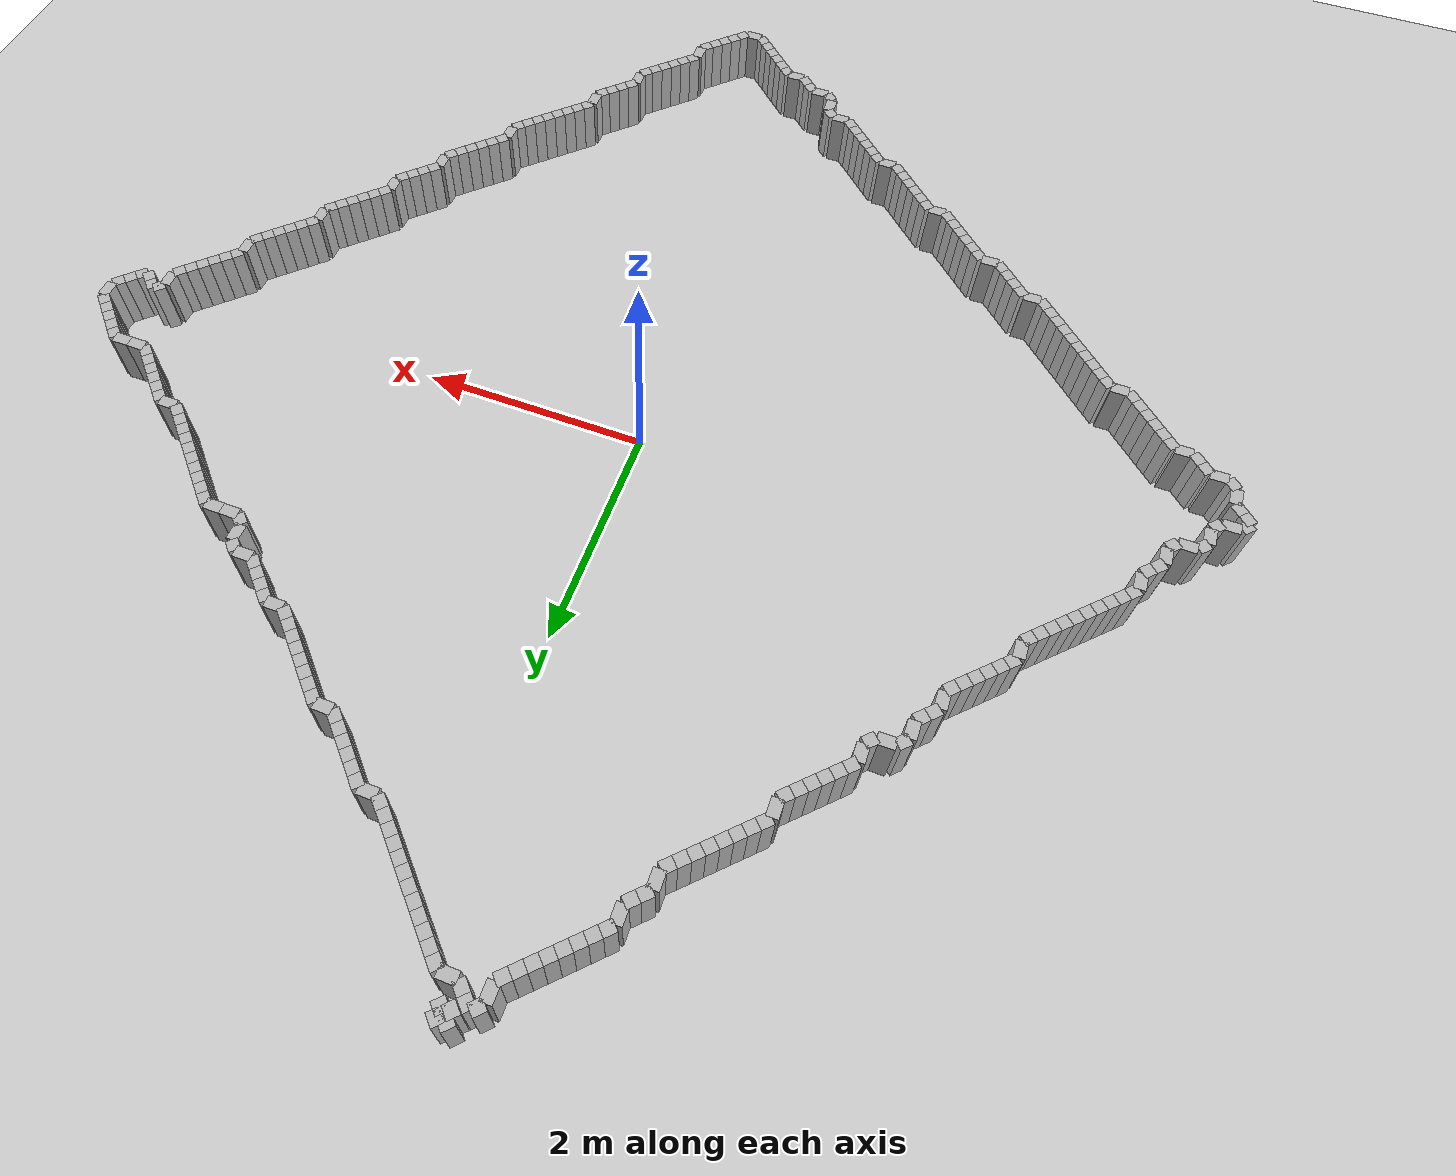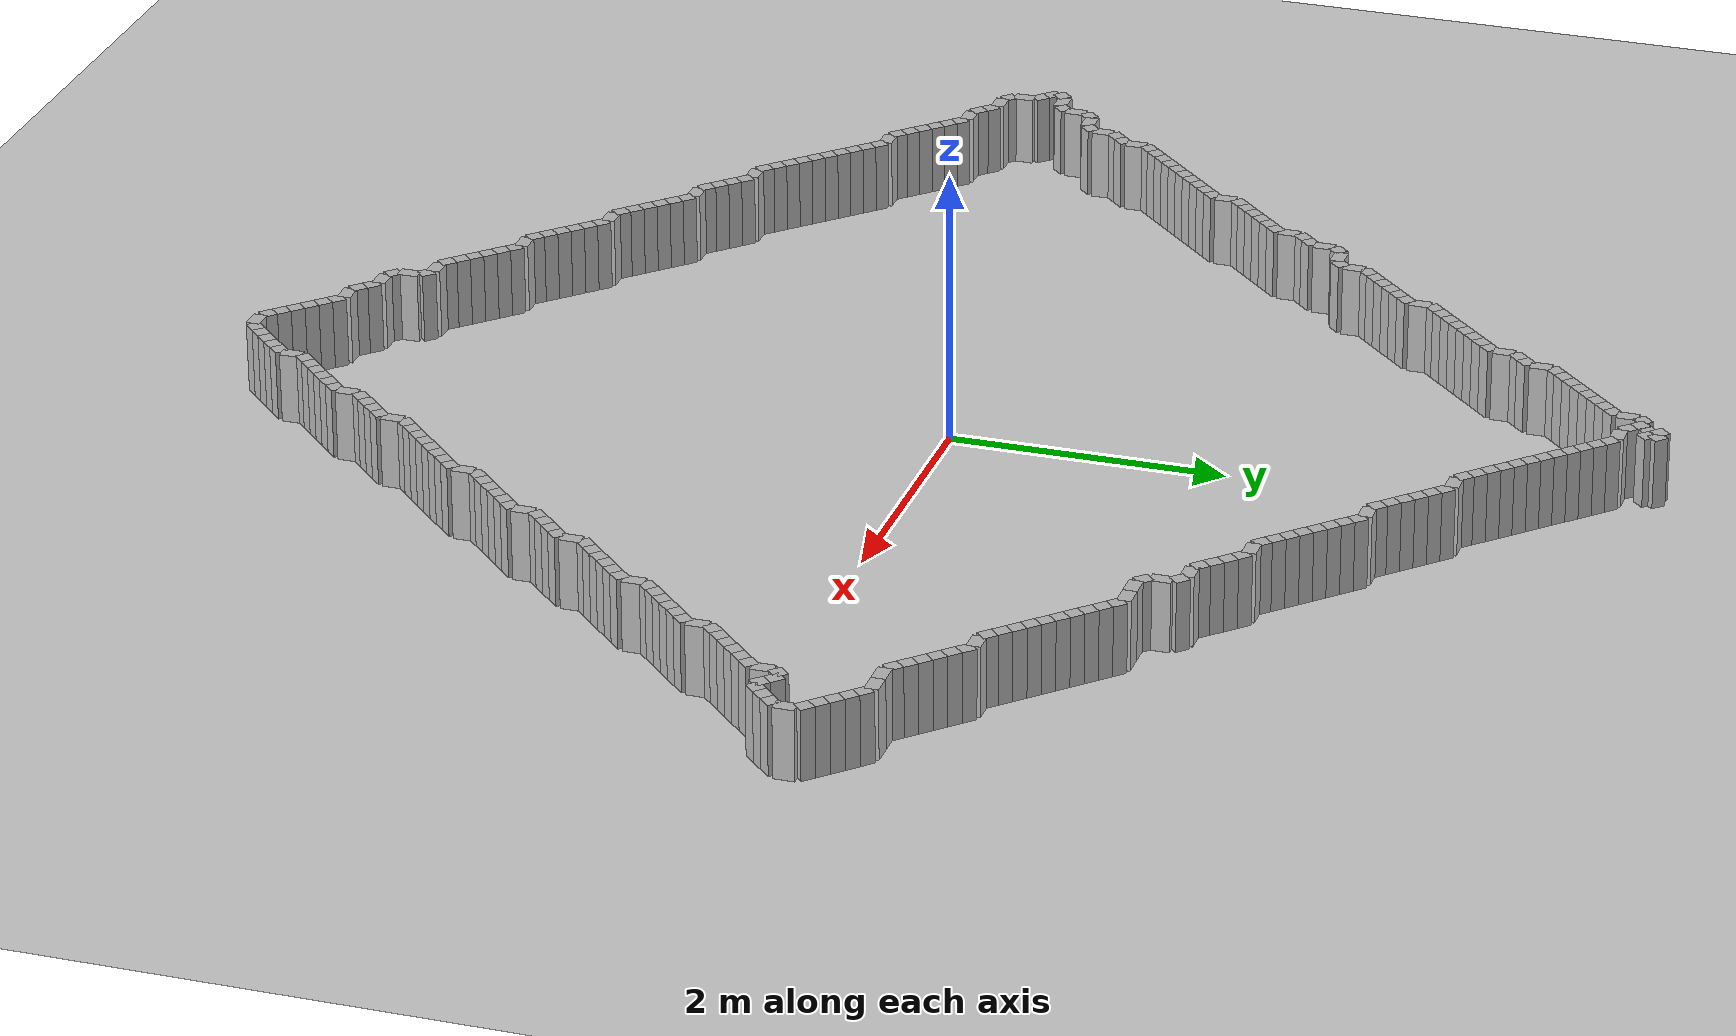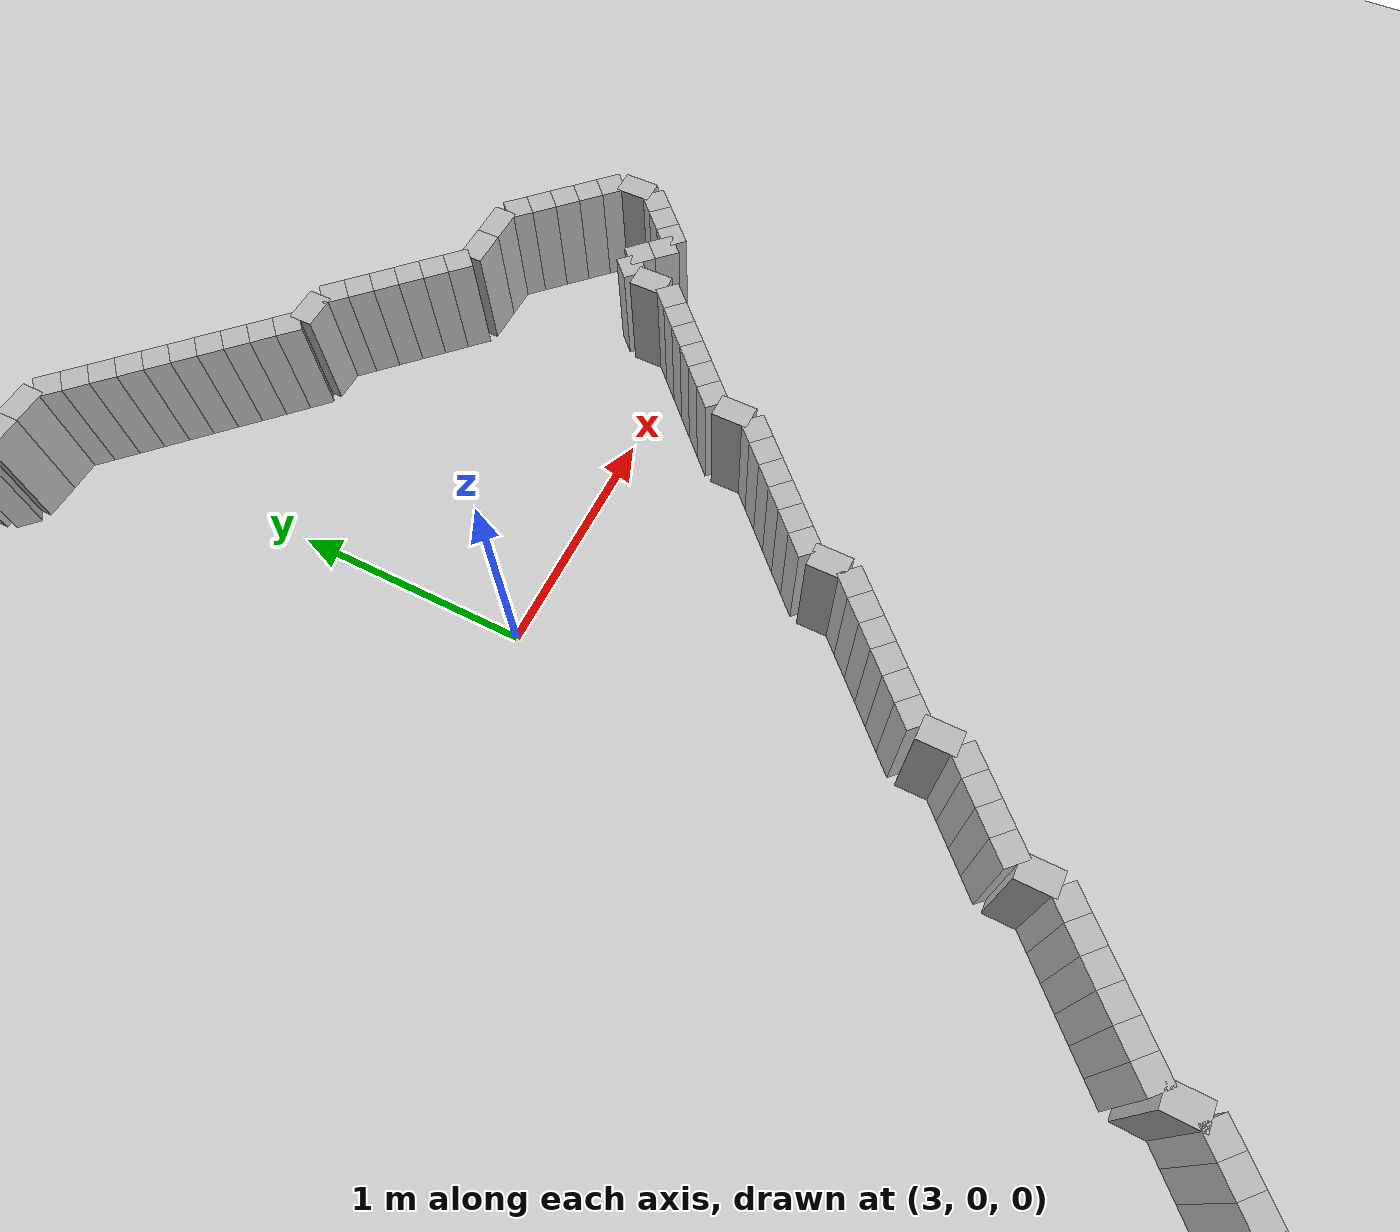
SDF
<?xml version="1.0" ?>
<!-- Gerado em 2025-05-06 23:36:20 -->
<sdf version="1.6">
  <world name="default">
    <include><uri>model://ground_plane</uri></include>
    <include><uri>model://sun</uri></include>

    <model name="wall_0">
      <static>true</static>
      <pose>0.4875 -4.9125 0 0 0 2.3562</pose>
      <link name="link">
        <visual name="vis">
          <geometry><box><size>0.1061 0.10 1.00</size></box></geometry>
        </visual>
        <collision name="col">
          <geometry><box><size>0.1061 0.10 1.00</size></box></geometry>
        </collision>
      </link>
    </model>

    <model name="wall_1">
      <static>true</static>
      <pose>0.4125 -4.8375 0 0 0 2.3562</pose>
      <link name="link">
        <visual name="vis">
          <geometry><box><size>0.1061 0.10 1.00</size></box></geometry>
        </visual>
        <collision name="col">
          <geometry><box><size>0.1061 0.10 1.00</size></box></geometry>
        </collision>
      </link>
    </model>

    <model name="wall_2">
      <static>true</static>
      <pose>0.3375 -4.7625 0 0 0 2.3562</pose>
      <link name="link">
        <visual name="vis">
          <geometry><box><size>0.1061 0.10 1.00</size></box></geometry>
        </visual>
        <collision name="col">
          <geometry><box><size>0.1061 0.10 1.00</size></box></geometry>
        </collision>
      </link>
    </model>

    <model name="wall_3">
      <static>true</static>
      <pose>0.2625 -4.6875 0 0 0 2.3562</pose>
      <link name="link">
        <visual name="vis">
          <geometry><box><size>0.1061 0.10 1.00</size></box></geometry>
        </visual>
        <collision name="col">
          <geometry><box><size>0.1061 0.10 1.00</size></box></geometry>
        </collision>
      </link>
    </model>

    <model name="wall_4">
      <static>true</static>
      <pose>0.1875 -4.6125 0 0 0 2.3562</pose>
      <link name="link">
        <visual name="vis">
          <geometry><box><size>0.1061 0.10 1.00</size></box></geometry>
        </visual>
        <collision name="col">
          <geometry><box><size>0.1061 0.10 1.00</size></box></geometry>
        </collision>
      </link>
    </model>

    <model name="wall_5">
      <static>true</static>
      <pose>0.1125 -4.5375 0 0 0 2.3562</pose>
      <link name="link">
        <visual name="vis">
          <geometry><box><size>0.1061 0.10 1.00</size></box></geometry>
        </visual>
        <collision name="col">
          <geometry><box><size>0.1061 0.10 1.00</size></box></geometry>
        </collision>
      </link>
    </model>

    <model name="wall_6">
      <static>true</static>
      <pose>0.0000 -4.5000 0 0 0 3.1416</pose>
      <link name="link">
        <visual name="vis">
          <geometry><box><size>0.1500 0.10 1.00</size></box></geometry>
        </visual>
        <collision name="col">
          <geometry><box><size>0.1500 0.10 1.00</size></box></geometry>
        </collision>
      </link>
    </model>

    <model name="wall_7">
      <static>true</static>
      <pose>-0.1125 -4.4625 0 0 0 2.3562</pose>
      <link name="link">
        <visual name="vis">
          <geometry><box><size>0.1061 0.10 1.00</size></box></geometry>
        </visual>
        <collision name="col">
          <geometry><box><size>0.1061 0.10 1.00</size></box></geometry>
        </collision>
      </link>
    </model>

    <model name="wall_8">
      <static>true</static>
      <pose>-0.1875 -4.3875 0 0 0 2.3562</pose>
      <link name="link">
        <visual name="vis">
          <geometry><box><size>0.1061 0.10 1.00</size></box></geometry>
        </visual>
        <collision name="col">
          <geometry><box><size>0.1061 0.10 1.00</size></box></geometry>
        </collision>
      </link>
    </model>

    <model name="wall_9">
      <static>true</static>
      <pose>-0.3000 -4.3500 0 0 0 3.1416</pose>
      <link name="link">
        <visual name="vis">
          <geometry><box><size>0.1500 0.10 1.00</size></box></geometry>
        </visual>
        <collision name="col">
          <geometry><box><size>0.1500 0.10 1.00</size></box></geometry>
        </collision>
      </link>
    </model>

    <model name="wall_10">
      <static>true</static>
      <pose>-0.4125 -4.3125 0 0 0 2.3562</pose>
      <link name="link">
        <visual name="vis">
          <geometry><box><size>0.1061 0.10 1.00</size></box></geometry>
        </visual>
        <collision name="col">
          <geometry><box><size>0.1061 0.10 1.00</size></box></geometry>
        </collision>
      </link>
    </model>

    <model name="wall_11">
      <static>true</static>
      <pose>-0.4500 -4.2000 0 0 0 1.5708</pose>
      <link name="link">
        <visual name="vis">
          <geometry><box><size>0.1500 0.10 1.00</size></box></geometry>
        </visual>
        <collision name="col">
          <geometry><box><size>0.1500 0.10 1.00</size></box></geometry>
        </collision>
      </link>
    </model>

    <model name="wall_12">
      <static>true</static>
      <pose>-0.4875 -4.0875 0 0 0 2.3562</pose>
      <link name="link">
        <visual name="vis">
          <geometry><box><size>0.1061 0.10 1.00</size></box></geometry>
        </visual>
        <collision name="col">
          <geometry><box><size>0.1061 0.10 1.00</size></box></geometry>
        </collision>
      </link>
    </model>

    <model name="wall_13">
      <static>true</static>
      <pose>-0.6000 -4.0500 0 0 0 3.1416</pose>
      <link name="link">
        <visual name="vis">
          <geometry><box><size>0.1500 0.10 1.00</size></box></geometry>
        </visual>
        <collision name="col">
          <geometry><box><size>0.1500 0.10 1.00</size></box></geometry>
        </collision>
      </link>
    </model>

    <model name="wall_14">
      <static>true</static>
      <pose>-0.7125 -4.0125 0 0 0 2.3562</pose>
      <link name="link">
        <visual name="vis">
          <geometry><box><size>0.1061 0.10 1.00</size></box></geometry>
        </visual>
        <collision name="col">
          <geometry><box><size>0.1061 0.10 1.00</size></box></geometry>
        </collision>
      </link>
    </model>

    <model name="wall_15">
      <static>true</static>
      <pose>-0.7875 -3.9375 0 0 0 2.3562</pose>
      <link name="link">
        <visual name="vis">
          <geometry><box><size>0.1061 0.10 1.00</size></box></geometry>
        </visual>
        <collision name="col">
          <geometry><box><size>0.1061 0.10 1.00</size></box></geometry>
        </collision>
      </link>
    </model>

    <model name="wall_16">
      <static>true</static>
      <pose>-0.8625 -3.8625 0 0 0 2.3562</pose>
      <link name="link">
        <visual name="vis">
          <geometry><box><size>0.1061 0.10 1.00</size></box></geometry>
        </visual>
        <collision name="col">
          <geometry><box><size>0.1061 0.10 1.00</size></box></geometry>
        </collision>
      </link>
    </model>

    <model name="wall_17">
      <static>true</static>
      <pose>-0.9375 -3.7875 0 0 0 2.3562</pose>
      <link name="link">
        <visual name="vis">
          <geometry><box><size>0.1061 0.10 1.00</size></box></geometry>
        </visual>
        <collision name="col">
          <geometry><box><size>0.1061 0.10 1.00</size></box></geometry>
        </collision>
      </link>
    </model>

    <model name="wall_18">
      <static>true</static>
      <pose>-1.0125 -3.7125 0 0 0 2.3562</pose>
      <link name="link">
        <visual name="vis">
          <geometry><box><size>0.1061 0.10 1.00</size></box></geometry>
        </visual>
        <collision name="col">
          <geometry><box><size>0.1061 0.10 1.00</size></box></geometry>
        </collision>
      </link>
    </model>

    <model name="wall_19">
      <static>true</static>
      <pose>-1.0875 -3.6375 0 0 0 2.3562</pose>
      <link name="link">
        <visual name="vis">
          <geometry><box><size>0.1061 0.10 1.00</size></box></geometry>
        </visual>
        <collision name="col">
          <geometry><box><size>0.1061 0.10 1.00</size></box></geometry>
        </collision>
      </link>
    </model>

    <model name="wall_20">
      <static>true</static>
      <pose>-1.2000 -3.6000 0 0 0 3.1416</pose>
      <link name="link">
        <visual name="vis">
          <geometry><box><size>0.1500 0.10 1.00</size></box></geometry>
        </visual>
        <collision name="col">
          <geometry><box><size>0.1500 0.10 1.00</size></box></geometry>
        </collision>
      </link>
    </model>

    <model name="wall_21">
      <static>true</static>
      <pose>-1.3125 -3.5625 0 0 0 2.3562</pose>
      <link name="link">
        <visual name="vis">
          <geometry><box><size>0.1061 0.10 1.00</size></box></geometry>
        </visual>
        <collision name="col">
          <geometry><box><size>0.1061 0.10 1.00</size></box></geometry>
        </collision>
      </link>
    </model>

    <model name="wall_22">
      <static>true</static>
      <pose>-1.3875 -3.4875 0 0 0 2.3562</pose>
      <link name="link">
        <visual name="vis">
          <geometry><box><size>0.1061 0.10 1.00</size></box></geometry>
        </visual>
        <collision name="col">
          <geometry><box><size>0.1061 0.10 1.00</size></box></geometry>
        </collision>
      </link>
    </model>

    <model name="wall_23">
      <static>true</static>
      <pose>-1.4625 -3.4125 0 0 0 2.3562</pose>
      <link name="link">
        <visual name="vis">
          <geometry><box><size>0.1061 0.10 1.00</size></box></geometry>
        </visual>
        <collision name="col">
          <geometry><box><size>0.1061 0.10 1.00</size></box></geometry>
        </collision>
      </link>
    </model>

    <model name="wall_24">
      <static>true</static>
      <pose>-1.5375 -3.3375 0 0 0 2.3562</pose>
      <link name="link">
        <visual name="vis">
          <geometry><box><size>0.1061 0.10 1.00</size></box></geometry>
        </visual>
        <collision name="col">
          <geometry><box><size>0.1061 0.10 1.00</size></box></geometry>
        </collision>
      </link>
    </model>

    <model name="wall_25">
      <static>true</static>
      <pose>-1.6125 -3.2625 0 0 0 2.3562</pose>
      <link name="link">
        <visual name="vis">
          <geometry><box><size>0.1061 0.10 1.00</size></box></geometry>
        </visual>
        <collision name="col">
          <geometry><box><size>0.1061 0.10 1.00</size></box></geometry>
        </collision>
      </link>
    </model>

    <model name="wall_26">
      <static>true</static>
      <pose>-1.6875 -3.1875 0 0 0 2.3562</pose>
      <link name="link">
        <visual name="vis">
          <geometry><box><size>0.1061 0.10 1.00</size></box></geometry>
        </visual>
        <collision name="col">
          <geometry><box><size>0.1061 0.10 1.00</size></box></geometry>
        </collision>
      </link>
    </model>

    <model name="wall_27">
      <static>true</static>
      <pose>-1.8000 -3.1500 0 0 0 3.1416</pose>
      <link name="link">
        <visual name="vis">
          <geometry><box><size>0.1500 0.10 1.00</size></box></geometry>
        </visual>
        <collision name="col">
          <geometry><box><size>0.1500 0.10 1.00</size></box></geometry>
        </collision>
      </link>
    </model>

    <model name="wall_28">
      <static>true</static>
      <pose>-1.9125 -3.1125 0 0 0 2.3562</pose>
      <link name="link">
        <visual name="vis">
          <geometry><box><size>0.1061 0.10 1.00</size></box></geometry>
        </visual>
        <collision name="col">
          <geometry><box><size>0.1061 0.10 1.00</size></box></geometry>
        </collision>
      </link>
    </model>

    <model name="wall_29">
      <static>true</static>
      <pose>-1.9875 -3.0375 0 0 0 2.3562</pose>
      <link name="link">
        <visual name="vis">
          <geometry><box><size>0.1061 0.10 1.00</size></box></geometry>
        </visual>
        <collision name="col">
          <geometry><box><size>0.1061 0.10 1.00</size></box></geometry>
        </collision>
      </link>
    </model>

    <model name="wall_30">
      <static>true</static>
      <pose>-2.0625 -2.9625 0 0 0 2.3562</pose>
      <link name="link">
        <visual name="vis">
          <geometry><box><size>0.1061 0.10 1.00</size></box></geometry>
        </visual>
        <collision name="col">
          <geometry><box><size>0.1061 0.10 1.00</size></box></geometry>
        </collision>
      </link>
    </model>

    <model name="wall_31">
      <static>true</static>
      <pose>-2.1375 -2.8875 0 0 0 2.3562</pose>
      <link name="link">
        <visual name="vis">
          <geometry><box><size>0.1061 0.10 1.00</size></box></geometry>
        </visual>
        <collision name="col">
          <geometry><box><size>0.1061 0.10 1.00</size></box></geometry>
        </collision>
      </link>
    </model>

    <model name="wall_32">
      <static>true</static>
      <pose>-2.2125 -2.8125 0 0 0 2.3562</pose>
      <link name="link">
        <visual name="vis">
          <geometry><box><size>0.1061 0.10 1.00</size></box></geometry>
        </visual>
        <collision name="col">
          <geometry><box><size>0.1061 0.10 1.00</size></box></geometry>
        </collision>
      </link>
    </model>

    <model name="wall_33">
      <static>true</static>
      <pose>-2.2875 -2.7375 0 0 0 2.3562</pose>
      <link name="link">
        <visual name="vis">
          <geometry><box><size>0.1061 0.10 1.00</size></box></geometry>
        </visual>
        <collision name="col">
          <geometry><box><size>0.1061 0.10 1.00</size></box></geometry>
        </collision>
      </link>
    </model>

    <model name="wall_34">
      <static>true</static>
      <pose>-2.4000 -2.7000 0 0 0 3.1416</pose>
      <link name="link">
        <visual name="vis">
          <geometry><box><size>0.1500 0.10 1.00</size></box></geometry>
        </visual>
        <collision name="col">
          <geometry><box><size>0.1500 0.10 1.00</size></box></geometry>
        </collision>
      </link>
    </model>

    <model name="wall_35">
      <static>true</static>
      <pose>-2.5125 -2.6625 0 0 0 2.3562</pose>
      <link name="link">
        <visual name="vis">
          <geometry><box><size>0.1061 0.10 1.00</size></box></geometry>
        </visual>
        <collision name="col">
          <geometry><box><size>0.1061 0.10 1.00</size></box></geometry>
        </collision>
      </link>
    </model>

    <model name="wall_36">
      <static>true</static>
      <pose>-2.5875 -2.5875 0 0 0 2.3562</pose>
      <link name="link">
        <visual name="vis">
          <geometry><box><size>0.1061 0.10 1.00</size></box></geometry>
        </visual>
        <collision name="col">
          <geometry><box><size>0.1061 0.10 1.00</size></box></geometry>
        </collision>
      </link>
    </model>

    <model name="wall_37">
      <static>true</static>
      <pose>-2.6625 -2.5125 0 0 0 2.3562</pose>
      <link name="link">
        <visual name="vis">
          <geometry><box><size>0.1061 0.10 1.00</size></box></geometry>
        </visual>
        <collision name="col">
          <geometry><box><size>0.1061 0.10 1.00</size></box></geometry>
        </collision>
      </link>
    </model>

    <model name="wall_38">
      <static>true</static>
      <pose>-2.7375 -2.4375 0 0 0 2.3562</pose>
      <link name="link">
        <visual name="vis">
          <geometry><box><size>0.1061 0.10 1.00</size></box></geometry>
        </visual>
        <collision name="col">
          <geometry><box><size>0.1061 0.10 1.00</size></box></geometry>
        </collision>
      </link>
    </model>

    <model name="wall_39">
      <static>true</static>
      <pose>-2.8500 -2.4000 0 0 0 3.1416</pose>
      <link name="link">
        <visual name="vis">
          <geometry><box><size>0.1500 0.10 1.00</size></box></geometry>
        </visual>
        <collision name="col">
          <geometry><box><size>0.1500 0.10 1.00</size></box></geometry>
        </collision>
      </link>
    </model>

    <model name="wall_40">
      <static>true</static>
      <pose>-2.9625 -2.3625 0 0 0 2.3562</pose>
      <link name="link">
        <visual name="vis">
          <geometry><box><size>0.1061 0.10 1.00</size></box></geometry>
        </visual>
        <collision name="col">
          <geometry><box><size>0.1061 0.10 1.00</size></box></geometry>
        </collision>
      </link>
    </model>

    <model name="wall_41">
      <static>true</static>
      <pose>-3.0375 -2.2875 0 0 0 2.3562</pose>
      <link name="link">
        <visual name="vis">
          <geometry><box><size>0.1061 0.10 1.00</size></box></geometry>
        </visual>
        <collision name="col">
          <geometry><box><size>0.1061 0.10 1.00</size></box></geometry>
        </collision>
      </link>
    </model>

    <model name="wall_42">
      <static>true</static>
      <pose>-3.1125 -2.2125 0 0 0 2.3562</pose>
      <link name="link">
        <visual name="vis">
          <geometry><box><size>0.1061 0.10 1.00</size></box></geometry>
        </visual>
        <collision name="col">
          <geometry><box><size>0.1061 0.10 1.00</size></box></geometry>
        </collision>
      </link>
    </model>

    <model name="wall_43">
      <static>true</static>
      <pose>-3.1875 -2.1375 0 0 0 2.3562</pose>
      <link name="link">
        <visual name="vis">
          <geometry><box><size>0.1061 0.10 1.00</size></box></geometry>
        </visual>
        <collision name="col">
          <geometry><box><size>0.1061 0.10 1.00</size></box></geometry>
        </collision>
      </link>
    </model>

    <model name="wall_44">
      <static>true</static>
      <pose>-3.2625 -2.0625 0 0 0 2.3562</pose>
      <link name="link">
        <visual name="vis">
          <geometry><box><size>0.1061 0.10 1.00</size></box></geometry>
        </visual>
        <collision name="col">
          <geometry><box><size>0.1061 0.10 1.00</size></box></geometry>
        </collision>
      </link>
    </model>

    <model name="wall_45">
      <static>true</static>
      <pose>-3.3375 -1.9875 0 0 0 2.3562</pose>
      <link name="link">
        <visual name="vis">
          <geometry><box><size>0.1061 0.10 1.00</size></box></geometry>
        </visual>
        <collision name="col">
          <geometry><box><size>0.1061 0.10 1.00</size></box></geometry>
        </collision>
      </link>
    </model>

    <model name="wall_46">
      <static>true</static>
      <pose>-3.4125 -1.9125 0 0 0 2.3562</pose>
      <link name="link">
        <visual name="vis">
          <geometry><box><size>0.1061 0.10 1.00</size></box></geometry>
        </visual>
        <collision name="col">
          <geometry><box><size>0.1061 0.10 1.00</size></box></geometry>
        </collision>
      </link>
    </model>

    <model name="wall_47">
      <static>true</static>
      <pose>-3.4875 -1.8375 0 0 0 2.3562</pose>
      <link name="link">
        <visual name="vis">
          <geometry><box><size>0.1061 0.10 1.00</size></box></geometry>
        </visual>
        <collision name="col">
          <geometry><box><size>0.1061 0.10 1.00</size></box></geometry>
        </collision>
      </link>
    </model>

    <model name="wall_48">
      <static>true</static>
      <pose>-3.5625 -1.7625 0 0 0 2.3562</pose>
      <link name="link">
        <visual name="vis">
          <geometry><box><size>0.1061 0.10 1.00</size></box></geometry>
        </visual>
        <collision name="col">
          <geometry><box><size>0.1061 0.10 1.00</size></box></geometry>
        </collision>
      </link>
    </model>

    <model name="wall_49">
      <static>true</static>
      <pose>-3.6375 -1.6875 0 0 0 2.3562</pose>
      <link name="link">
        <visual name="vis">
          <geometry><box><size>0.1061 0.10 1.00</size></box></geometry>
        </visual>
        <collision name="col">
          <geometry><box><size>0.1061 0.10 1.00</size></box></geometry>
        </collision>
      </link>
    </model>

    <model name="wall_50">
      <static>true</static>
      <pose>-3.7500 -1.6500 0 0 0 3.1416</pose>
      <link name="link">
        <visual name="vis">
          <geometry><box><size>0.1500 0.10 1.00</size></box></geometry>
        </visual>
        <collision name="col">
          <geometry><box><size>0.1500 0.10 1.00</size></box></geometry>
        </collision>
      </link>
    </model>

    <model name="wall_51">
      <static>true</static>
      <pose>-3.8625 -1.6125 0 0 0 2.3562</pose>
      <link name="link">
        <visual name="vis">
          <geometry><box><size>0.1061 0.10 1.00</size></box></geometry>
        </visual>
        <collision name="col">
          <geometry><box><size>0.1061 0.10 1.00</size></box></geometry>
        </collision>
      </link>
    </model>

    <model name="wall_52">
      <static>true</static>
      <pose>-3.9375 -1.5375 0 0 0 2.3562</pose>
      <link name="link">
        <visual name="vis">
          <geometry><box><size>0.1061 0.10 1.00</size></box></geometry>
        </visual>
        <collision name="col">
          <geometry><box><size>0.1061 0.10 1.00</size></box></geometry>
        </collision>
      </link>
    </model>

    <model name="wall_53">
      <static>true</static>
      <pose>-4.0125 -1.4625 0 0 0 2.3562</pose>
      <link name="link">
        <visual name="vis">
          <geometry><box><size>0.1061 0.10 1.00</size></box></geometry>
        </visual>
        <collision name="col">
          <geometry><box><size>0.1061 0.10 1.00</size></box></geometry>
        </collision>
      </link>
    </model>

    <model name="wall_54">
      <static>true</static>
      <pose>-4.0875 -1.3875 0 0 0 2.3562</pose>
      <link name="link">
        <visual name="vis">
          <geometry><box><size>0.1061 0.10 1.00</size></box></geometry>
        </visual>
        <collision name="col">
          <geometry><box><size>0.1061 0.10 1.00</size></box></geometry>
        </collision>
      </link>
    </model>

    <model name="wall_55">
      <static>true</static>
      <pose>-4.1625 -1.3125 0 0 0 2.3562</pose>
      <link name="link">
        <visual name="vis">
          <geometry><box><size>0.1061 0.10 1.00</size></box></geometry>
        </visual>
        <collision name="col">
          <geometry><box><size>0.1061 0.10 1.00</size></box></geometry>
        </collision>
      </link>
    </model>

    <model name="wall_56">
      <static>true</static>
      <pose>-4.2375 -1.2375 0 0 0 2.3562</pose>
      <link name="link">
        <visual name="vis">
          <geometry><box><size>0.1061 0.10 1.00</size></box></geometry>
        </visual>
        <collision name="col">
          <geometry><box><size>0.1061 0.10 1.00</size></box></geometry>
        </collision>
      </link>
    </model>

    <model name="wall_57">
      <static>true</static>
      <pose>-4.3500 -1.2000 0 0 0 3.1416</pose>
      <link name="link">
        <visual name="vis">
          <geometry><box><size>0.1500 0.10 1.00</size></box></geometry>
        </visual>
        <collision name="col">
          <geometry><box><size>0.1500 0.10 1.00</size></box></geometry>
        </collision>
      </link>
    </model>

    <model name="wall_58">
      <static>true</static>
      <pose>-4.4625 -1.1625 0 0 0 2.3562</pose>
      <link name="link">
        <visual name="vis">
          <geometry><box><size>0.1061 0.10 1.00</size></box></geometry>
        </visual>
        <collision name="col">
          <geometry><box><size>0.1061 0.10 1.00</size></box></geometry>
        </collision>
      </link>
    </model>

    <model name="wall_59">
      <static>true</static>
      <pose>-4.5375 -1.0875 0 0 0 2.3562</pose>
      <link name="link">
        <visual name="vis">
          <geometry><box><size>0.1061 0.10 1.00</size></box></geometry>
        </visual>
        <collision name="col">
          <geometry><box><size>0.1061 0.10 1.00</size></box></geometry>
        </collision>
      </link>
    </model>

    <model name="wall_60">
      <static>true</static>
      <pose>-4.6500 -1.0500 0 0 0 3.1416</pose>
      <link name="link">
        <visual name="vis">
          <geometry><box><size>0.1500 0.10 1.00</size></box></geometry>
        </visual>
        <collision name="col">
          <geometry><box><size>0.1500 0.10 1.00</size></box></geometry>
        </collision>
      </link>
    </model>

    <model name="wall_61">
      <static>true</static>
      <pose>-4.7625 -1.0125 0 0 0 2.3562</pose>
      <link name="link">
        <visual name="vis">
          <geometry><box><size>0.1061 0.10 1.00</size></box></geometry>
        </visual>
        <collision name="col">
          <geometry><box><size>0.1061 0.10 1.00</size></box></geometry>
        </collision>
      </link>
    </model>

    <model name="wall_62">
      <static>true</static>
      <pose>-4.8000 -0.9000 0 0 0 1.5708</pose>
      <link name="link">
        <visual name="vis">
          <geometry><box><size>0.1500 0.10 1.00</size></box></geometry>
        </visual>
        <collision name="col">
          <geometry><box><size>0.1500 0.10 1.00</size></box></geometry>
        </collision>
      </link>
    </model>

    <model name="wall_63">
      <static>true</static>
      <pose>-4.8375 -0.7875 0 0 0 2.3562</pose>
      <link name="link">
        <visual name="vis">
          <geometry><box><size>0.1061 0.10 1.00</size></box></geometry>
        </visual>
        <collision name="col">
          <geometry><box><size>0.1061 0.10 1.00</size></box></geometry>
        </collision>
      </link>
    </model>

    <model name="wall_64">
      <static>true</static>
      <pose>-4.9125 -0.7125 0 0 0 2.3562</pose>
      <link name="link">
        <visual name="vis">
          <geometry><box><size>0.1061 0.10 1.00</size></box></geometry>
        </visual>
        <collision name="col">
          <geometry><box><size>0.1061 0.10 1.00</size></box></geometry>
        </collision>
      </link>
    </model>

    <model name="wall_65">
      <static>true</static>
      <pose>-4.9125 -0.6375 0 0 0 0.7854</pose>
      <link name="link">
        <visual name="vis">
          <geometry><box><size>0.1061 0.10 1.00</size></box></geometry>
        </visual>
        <collision name="col">
          <geometry><box><size>0.1061 0.10 1.00</size></box></geometry>
        </collision>
      </link>
    </model>

    <model name="wall_66">
      <static>true</static>
      <pose>-4.8000 -0.6000 0 0 0 0.0000</pose>
      <link name="link">
        <visual name="vis">
          <geometry><box><size>0.1500 0.10 1.00</size></box></geometry>
        </visual>
        <collision name="col">
          <geometry><box><size>0.1500 0.10 1.00</size></box></geometry>
        </collision>
      </link>
    </model>

    <model name="wall_67">
      <static>true</static>
      <pose>-4.6875 -0.5625 0 0 0 0.7854</pose>
      <link name="link">
        <visual name="vis">
          <geometry><box><size>0.1061 0.10 1.00</size></box></geometry>
        </visual>
        <collision name="col">
          <geometry><box><size>0.1061 0.10 1.00</size></box></geometry>
        </collision>
      </link>
    </model>

    <model name="wall_68">
      <static>true</static>
      <pose>-4.6500 -0.4500 0 0 0 1.5708</pose>
      <link name="link">
        <visual name="vis">
          <geometry><box><size>0.1500 0.10 1.00</size></box></geometry>
        </visual>
        <collision name="col">
          <geometry><box><size>0.1500 0.10 1.00</size></box></geometry>
        </collision>
      </link>
    </model>

    <model name="wall_69">
      <static>true</static>
      <pose>-4.6125 -0.3375 0 0 0 0.7854</pose>
      <link name="link">
        <visual name="vis">
          <geometry><box><size>0.1061 0.10 1.00</size></box></geometry>
        </visual>
        <collision name="col">
          <geometry><box><size>0.1061 0.10 1.00</size></box></geometry>
        </collision>
      </link>
    </model>

    <model name="wall_70">
      <static>true</static>
      <pose>-4.5000 -0.3000 0 0 0 0.0000</pose>
      <link name="link">
        <visual name="vis">
          <geometry><box><size>0.1500 0.10 1.00</size></box></geometry>
        </visual>
        <collision name="col">
          <geometry><box><size>0.1500 0.10 1.00</size></box></geometry>
        </collision>
      </link>
    </model>

    <model name="wall_71">
      <static>true</static>
      <pose>-4.3875 -0.2625 0 0 0 0.7854</pose>
      <link name="link">
        <visual name="vis">
          <geometry><box><size>0.1061 0.10 1.00</size></box></geometry>
        </visual>
        <collision name="col">
          <geometry><box><size>0.1061 0.10 1.00</size></box></geometry>
        </collision>
      </link>
    </model>

    <model name="wall_72">
      <static>true</static>
      <pose>-4.3500 -0.1500 0 0 0 1.5708</pose>
      <link name="link">
        <visual name="vis">
          <geometry><box><size>0.1500 0.10 1.00</size></box></geometry>
        </visual>
        <collision name="col">
          <geometry><box><size>0.1500 0.10 1.00</size></box></geometry>
        </collision>
      </link>
    </model>

    <model name="wall_73">
      <static>true</static>
      <pose>-4.3125 -0.0375 0 0 0 0.7854</pose>
      <link name="link">
        <visual name="vis">
          <geometry><box><size>0.1061 0.10 1.00</size></box></geometry>
        </visual>
        <collision name="col">
          <geometry><box><size>0.1061 0.10 1.00</size></box></geometry>
        </collision>
      </link>
    </model>

    <model name="wall_74">
      <static>true</static>
      <pose>-4.2375 0.0375 0 0 0 0.7854</pose>
      <link name="link">
        <visual name="vis">
          <geometry><box><size>0.1061 0.10 1.00</size></box></geometry>
        </visual>
        <collision name="col">
          <geometry><box><size>0.1061 0.10 1.00</size></box></geometry>
        </collision>
      </link>
    </model>

    <model name="wall_75">
      <static>true</static>
      <pose>-4.2000 0.1500 0 0 0 1.5708</pose>
      <link name="link">
        <visual name="vis">
          <geometry><box><size>0.1500 0.10 1.00</size></box></geometry>
        </visual>
        <collision name="col">
          <geometry><box><size>0.1500 0.10 1.00</size></box></geometry>
        </collision>
      </link>
    </model>

    <model name="wall_76">
      <static>true</static>
      <pose>-4.1625 0.2625 0 0 0 0.7854</pose>
      <link name="link">
        <visual name="vis">
          <geometry><box><size>0.1061 0.10 1.00</size></box></geometry>
        </visual>
        <collision name="col">
          <geometry><box><size>0.1061 0.10 1.00</size></box></geometry>
        </collision>
      </link>
    </model>

    <model name="wall_77">
      <static>true</static>
      <pose>-4.0875 0.3375 0 0 0 0.7854</pose>
      <link name="link">
        <visual name="vis">
          <geometry><box><size>0.1061 0.10 1.00</size></box></geometry>
        </visual>
        <collision name="col">
          <geometry><box><size>0.1061 0.10 1.00</size></box></geometry>
        </collision>
      </link>
    </model>

    <model name="wall_78">
      <static>true</static>
      <pose>-4.0125 0.4125 0 0 0 0.7854</pose>
      <link name="link">
        <visual name="vis">
          <geometry><box><size>0.1061 0.10 1.00</size></box></geometry>
        </visual>
        <collision name="col">
          <geometry><box><size>0.1061 0.10 1.00</size></box></geometry>
        </collision>
      </link>
    </model>

    <model name="wall_79">
      <static>true</static>
      <pose>-3.9375 0.4875 0 0 0 0.7854</pose>
      <link name="link">
        <visual name="vis">
          <geometry><box><size>0.1061 0.10 1.00</size></box></geometry>
        </visual>
        <collision name="col">
          <geometry><box><size>0.1061 0.10 1.00</size></box></geometry>
        </collision>
      </link>
    </model>

    <model name="wall_80">
      <static>true</static>
      <pose>-3.8625 0.5625 0 0 0 0.7854</pose>
      <link name="link">
        <visual name="vis">
          <geometry><box><size>0.1061 0.10 1.00</size></box></geometry>
        </visual>
        <collision name="col">
          <geometry><box><size>0.1061 0.10 1.00</size></box></geometry>
        </collision>
      </link>
    </model>

    <model name="wall_81">
      <static>true</static>
      <pose>-3.7875 0.6375 0 0 0 0.7854</pose>
      <link name="link">
        <visual name="vis">
          <geometry><box><size>0.1061 0.10 1.00</size></box></geometry>
        </visual>
        <collision name="col">
          <geometry><box><size>0.1061 0.10 1.00</size></box></geometry>
        </collision>
      </link>
    </model>

    <model name="wall_82">
      <static>true</static>
      <pose>-3.7125 0.7125 0 0 0 0.7854</pose>
      <link name="link">
        <visual name="vis">
          <geometry><box><size>0.1061 0.10 1.00</size></box></geometry>
        </visual>
        <collision name="col">
          <geometry><box><size>0.1061 0.10 1.00</size></box></geometry>
        </collision>
      </link>
    </model>

    <model name="wall_83">
      <static>true</static>
      <pose>-3.6375 0.7875 0 0 0 0.7854</pose>
      <link name="link">
        <visual name="vis">
          <geometry><box><size>0.1061 0.10 1.00</size></box></geometry>
        </visual>
        <collision name="col">
          <geometry><box><size>0.1061 0.10 1.00</size></box></geometry>
        </collision>
      </link>
    </model>

    <model name="wall_84">
      <static>true</static>
      <pose>-3.5625 0.8625 0 0 0 0.7854</pose>
      <link name="link">
        <visual name="vis">
          <geometry><box><size>0.1061 0.10 1.00</size></box></geometry>
        </visual>
        <collision name="col">
          <geometry><box><size>0.1061 0.10 1.00</size></box></geometry>
        </collision>
      </link>
    </model>

    <model name="wall_85">
      <static>true</static>
      <pose>-3.4875 0.9375 0 0 0 0.7854</pose>
      <link name="link">
        <visual name="vis">
          <geometry><box><size>0.1061 0.10 1.00</size></box></geometry>
        </visual>
        <collision name="col">
          <geometry><box><size>0.1061 0.10 1.00</size></box></geometry>
        </collision>
      </link>
    </model>

    <model name="wall_86">
      <static>true</static>
      <pose>-3.4500 1.0500 0 0 0 1.5708</pose>
      <link name="link">
        <visual name="vis">
          <geometry><box><size>0.1500 0.10 1.00</size></box></geometry>
        </visual>
        <collision name="col">
          <geometry><box><size>0.1500 0.10 1.00</size></box></geometry>
        </collision>
      </link>
    </model>

    <model name="wall_87">
      <static>true</static>
      <pose>-3.4125 1.1625 0 0 0 0.7854</pose>
      <link name="link">
        <visual name="vis">
          <geometry><box><size>0.1061 0.10 1.00</size></box></geometry>
        </visual>
        <collision name="col">
          <geometry><box><size>0.1061 0.10 1.00</size></box></geometry>
        </collision>
      </link>
    </model>

    <model name="wall_88">
      <static>true</static>
      <pose>-3.3375 1.2375 0 0 0 0.7854</pose>
      <link name="link">
        <visual name="vis">
          <geometry><box><size>0.1061 0.10 1.00</size></box></geometry>
        </visual>
        <collision name="col">
          <geometry><box><size>0.1061 0.10 1.00</size></box></geometry>
        </collision>
      </link>
    </model>

    <model name="wall_89">
      <static>true</static>
      <pose>-3.2625 1.3125 0 0 0 0.7854</pose>
      <link name="link">
        <visual name="vis">
          <geometry><box><size>0.1061 0.10 1.00</size></box></geometry>
        </visual>
        <collision name="col">
          <geometry><box><size>0.1061 0.10 1.00</size></box></geometry>
        </collision>
      </link>
    </model>

    <model name="wall_90">
      <static>true</static>
      <pose>-3.1875 1.3875 0 0 0 0.7854</pose>
      <link name="link">
        <visual name="vis">
          <geometry><box><size>0.1061 0.10 1.00</size></box></geometry>
        </visual>
        <collision name="col">
          <geometry><box><size>0.1061 0.10 1.00</size></box></geometry>
        </collision>
      </link>
    </model>

    <model name="wall_91">
      <static>true</static>
      <pose>-3.1125 1.4625 0 0 0 0.7854</pose>
      <link name="link">
        <visual name="vis">
          <geometry><box><size>0.1061 0.10 1.00</size></box></geometry>
        </visual>
        <collision name="col">
          <geometry><box><size>0.1061 0.10 1.00</size></box></geometry>
        </collision>
      </link>
    </model>

    <model name="wall_92">
      <static>true</static>
      <pose>-3.0375 1.5375 0 0 0 0.7854</pose>
      <link name="link">
        <visual name="vis">
          <geometry><box><size>0.1061 0.10 1.00</size></box></geometry>
        </visual>
        <collision name="col">
          <geometry><box><size>0.1061 0.10 1.00</size></box></geometry>
        </collision>
      </link>
    </model>

    <model name="wall_93">
      <static>true</static>
      <pose>-3.0000 1.6500 0 0 0 1.5708</pose>
      <link name="link">
        <visual name="vis">
          <geometry><box><size>0.1500 0.10 1.00</size></box></geometry>
        </visual>
        <collision name="col">
          <geometry><box><size>0.1500 0.10 1.00</size></box></geometry>
        </collision>
      </link>
    </model>

    <model name="wall_94">
      <static>true</static>
      <pose>-2.9625 1.7625 0 0 0 0.7854</pose>
      <link name="link">
        <visual name="vis">
          <geometry><box><size>0.1061 0.10 1.00</size></box></geometry>
        </visual>
        <collision name="col">
          <geometry><box><size>0.1061 0.10 1.00</size></box></geometry>
        </collision>
      </link>
    </model>

    <model name="wall_95">
      <static>true</static>
      <pose>-2.8875 1.8375 0 0 0 0.7854</pose>
      <link name="link">
        <visual name="vis">
          <geometry><box><size>0.1061 0.10 1.00</size></box></geometry>
        </visual>
        <collision name="col">
          <geometry><box><size>0.1061 0.10 1.00</size></box></geometry>
        </collision>
      </link>
    </model>

    <model name="wall_96">
      <static>true</static>
      <pose>-2.8500 1.9500 0 0 0 1.5708</pose>
      <link name="link">
        <visual name="vis">
          <geometry><box><size>0.1500 0.10 1.00</size></box></geometry>
        </visual>
        <collision name="col">
          <geometry><box><size>0.1500 0.10 1.00</size></box></geometry>
        </collision>
      </link>
    </model>

    <model name="wall_97">
      <static>true</static>
      <pose>-2.8125 2.0625 0 0 0 0.7854</pose>
      <link name="link">
        <visual name="vis">
          <geometry><box><size>0.1061 0.10 1.00</size></box></geometry>
        </visual>
        <collision name="col">
          <geometry><box><size>0.1061 0.10 1.00</size></box></geometry>
        </collision>
      </link>
    </model>

    <model name="wall_98">
      <static>true</static>
      <pose>-2.7000 2.1000 0 0 0 0.0000</pose>
      <link name="link">
        <visual name="vis">
          <geometry><box><size>0.1500 0.10 1.00</size></box></geometry>
        </visual>
        <collision name="col">
          <geometry><box><size>0.1500 0.10 1.00</size></box></geometry>
        </collision>
      </link>
    </model>

    <model name="wall_99">
      <static>true</static>
      <pose>-2.5875 2.1375 0 0 0 0.7854</pose>
      <link name="link">
        <visual name="vis">
          <geometry><box><size>0.1061 0.10 1.00</size></box></geometry>
        </visual>
        <collision name="col">
          <geometry><box><size>0.1061 0.10 1.00</size></box></geometry>
        </collision>
      </link>
    </model>

    <model name="wall_100">
      <static>true</static>
      <pose>-2.5500 2.2500 0 0 0 1.5708</pose>
      <link name="link">
        <visual name="vis">
          <geometry><box><size>0.1500 0.10 1.00</size></box></geometry>
        </visual>
        <collision name="col">
          <geometry><box><size>0.1500 0.10 1.00</size></box></geometry>
        </collision>
      </link>
    </model>

    <model name="wall_101">
      <static>true</static>
      <pose>-2.5125 2.3625 0 0 0 0.7854</pose>
      <link name="link">
        <visual name="vis">
          <geometry><box><size>0.1061 0.10 1.00</size></box></geometry>
        </visual>
        <collision name="col">
          <geometry><box><size>0.1061 0.10 1.00</size></box></geometry>
        </collision>
      </link>
    </model>

    <model name="wall_102">
      <static>true</static>
      <pose>-2.4375 2.4375 0 0 0 0.7854</pose>
      <link name="link">
        <visual name="vis">
          <geometry><box><size>0.1061 0.10 1.00</size></box></geometry>
        </visual>
        <collision name="col">
          <geometry><box><size>0.1061 0.10 1.00</size></box></geometry>
        </collision>
      </link>
    </model>

    <model name="wall_103">
      <static>true</static>
      <pose>-2.3625 2.5125 0 0 0 0.7854</pose>
      <link name="link">
        <visual name="vis">
          <geometry><box><size>0.1061 0.10 1.00</size></box></geometry>
        </visual>
        <collision name="col">
          <geometry><box><size>0.1061 0.10 1.00</size></box></geometry>
        </collision>
      </link>
    </model>

    <model name="wall_104">
      <static>true</static>
      <pose>-2.2875 2.5875 0 0 0 0.7854</pose>
      <link name="link">
        <visual name="vis">
          <geometry><box><size>0.1061 0.10 1.00</size></box></geometry>
        </visual>
        <collision name="col">
          <geometry><box><size>0.1061 0.10 1.00</size></box></geometry>
        </collision>
      </link>
    </model>

    <model name="wall_105">
      <static>true</static>
      <pose>-2.2125 2.6625 0 0 0 0.7854</pose>
      <link name="link">
        <visual name="vis">
          <geometry><box><size>0.1061 0.10 1.00</size></box></geometry>
        </visual>
        <collision name="col">
          <geometry><box><size>0.1061 0.10 1.00</size></box></geometry>
        </collision>
      </link>
    </model>

    <model name="wall_106">
      <static>true</static>
      <pose>-2.1375 2.7375 0 0 0 0.7854</pose>
      <link name="link">
        <visual name="vis">
          <geometry><box><size>0.1061 0.10 1.00</size></box></geometry>
        </visual>
        <collision name="col">
          <geometry><box><size>0.1061 0.10 1.00</size></box></geometry>
        </collision>
      </link>
    </model>

    <model name="wall_107">
      <static>true</static>
      <pose>-2.1000 2.8500 0 0 0 1.5708</pose>
      <link name="link">
        <visual name="vis">
          <geometry><box><size>0.1500 0.10 1.00</size></box></geometry>
        </visual>
        <collision name="col">
          <geometry><box><size>0.1500 0.10 1.00</size></box></geometry>
        </collision>
      </link>
    </model>

    <model name="wall_108">
      <static>true</static>
      <pose>-2.0625 2.9625 0 0 0 0.7854</pose>
      <link name="link">
        <visual name="vis">
          <geometry><box><size>0.1061 0.10 1.00</size></box></geometry>
        </visual>
        <collision name="col">
          <geometry><box><size>0.1061 0.10 1.00</size></box></geometry>
        </collision>
      </link>
    </model>

    <model name="wall_109">
      <static>true</static>
      <pose>-1.9875 3.0375 0 0 0 0.7854</pose>
      <link name="link">
        <visual name="vis">
          <geometry><box><size>0.1061 0.10 1.00</size></box></geometry>
        </visual>
        <collision name="col">
          <geometry><box><size>0.1061 0.10 1.00</size></box></geometry>
        </collision>
      </link>
    </model>

    <model name="wall_110">
      <static>true</static>
      <pose>-1.9125 3.1125 0 0 0 0.7854</pose>
      <link name="link">
        <visual name="vis">
          <geometry><box><size>0.1061 0.10 1.00</size></box></geometry>
        </visual>
        <collision name="col">
          <geometry><box><size>0.1061 0.10 1.00</size></box></geometry>
        </collision>
      </link>
    </model>

    <model name="wall_111">
      <static>true</static>
      <pose>-1.8375 3.1875 0 0 0 0.7854</pose>
      <link name="link">
        <visual name="vis">
          <geometry><box><size>0.1061 0.10 1.00</size></box></geometry>
        </visual>
        <collision name="col">
          <geometry><box><size>0.1061 0.10 1.00</size></box></geometry>
        </collision>
      </link>
    </model>

    <model name="wall_112">
      <static>true</static>
      <pose>-1.7625 3.2625 0 0 0 0.7854</pose>
      <link name="link">
        <visual name="vis">
          <geometry><box><size>0.1061 0.10 1.00</size></box></geometry>
        </visual>
        <collision name="col">
          <geometry><box><size>0.1061 0.10 1.00</size></box></geometry>
        </collision>
      </link>
    </model>

    <model name="wall_113">
      <static>true</static>
      <pose>-1.6875 3.3375 0 0 0 0.7854</pose>
      <link name="link">
        <visual name="vis">
          <geometry><box><size>0.1061 0.10 1.00</size></box></geometry>
        </visual>
        <collision name="col">
          <geometry><box><size>0.1061 0.10 1.00</size></box></geometry>
        </collision>
      </link>
    </model>

    <model name="wall_114">
      <static>true</static>
      <pose>-1.6125 3.4125 0 0 0 0.7854</pose>
      <link name="link">
        <visual name="vis">
          <geometry><box><size>0.1061 0.10 1.00</size></box></geometry>
        </visual>
        <collision name="col">
          <geometry><box><size>0.1061 0.10 1.00</size></box></geometry>
        </collision>
      </link>
    </model>

    <model name="wall_115">
      <static>true</static>
      <pose>-1.5375 3.4875 0 0 0 0.7854</pose>
      <link name="link">
        <visual name="vis">
          <geometry><box><size>0.1061 0.10 1.00</size></box></geometry>
        </visual>
        <collision name="col">
          <geometry><box><size>0.1061 0.10 1.00</size></box></geometry>
        </collision>
      </link>
    </model>

    <model name="wall_116">
      <static>true</static>
      <pose>-1.5000 3.6000 0 0 0 1.5708</pose>
      <link name="link">
        <visual name="vis">
          <geometry><box><size>0.1500 0.10 1.00</size></box></geometry>
        </visual>
        <collision name="col">
          <geometry><box><size>0.1500 0.10 1.00</size></box></geometry>
        </collision>
      </link>
    </model>

    <model name="wall_117">
      <static>true</static>
      <pose>-1.4625 3.7125 0 0 0 0.7854</pose>
      <link name="link">
        <visual name="vis">
          <geometry><box><size>0.1061 0.10 1.00</size></box></geometry>
        </visual>
        <collision name="col">
          <geometry><box><size>0.1061 0.10 1.00</size></box></geometry>
        </collision>
      </link>
    </model>

    <model name="wall_118">
      <static>true</static>
      <pose>-1.3875 3.7875 0 0 0 0.7854</pose>
      <link name="link">
        <visual name="vis">
          <geometry><box><size>0.1061 0.10 1.00</size></box></geometry>
        </visual>
        <collision name="col">
          <geometry><box><size>0.1061 0.10 1.00</size></box></geometry>
        </collision>
      </link>
    </model>

    <model name="wall_119">
      <static>true</static>
      <pose>-1.3500 3.9000 0 0 0 1.5708</pose>
      <link name="link">
        <visual name="vis">
          <geometry><box><size>0.1500 0.10 1.00</size></box></geometry>
        </visual>
        <collision name="col">
          <geometry><box><size>0.1500 0.10 1.00</size></box></geometry>
        </collision>
      </link>
    </model>

    <model name="wall_120">
      <static>true</static>
      <pose>-1.3125 4.0125 0 0 0 0.7854</pose>
      <link name="link">
        <visual name="vis">
          <geometry><box><size>0.1061 0.10 1.00</size></box></geometry>
        </visual>
        <collision name="col">
          <geometry><box><size>0.1061 0.10 1.00</size></box></geometry>
        </collision>
      </link>
    </model>

    <model name="wall_121">
      <static>true</static>
      <pose>-1.2375 4.0875 0 0 0 0.7854</pose>
      <link name="link">
        <visual name="vis">
          <geometry><box><size>0.1061 0.10 1.00</size></box></geometry>
        </visual>
        <collision name="col">
          <geometry><box><size>0.1061 0.10 1.00</size></box></geometry>
        </collision>
      </link>
    </model>

    <model name="wall_122">
      <static>true</static>
      <pose>-1.1625 4.1625 0 0 0 0.7854</pose>
      <link name="link">
        <visual name="vis">
          <geometry><box><size>0.1061 0.10 1.00</size></box></geometry>
        </visual>
        <collision name="col">
          <geometry><box><size>0.1061 0.10 1.00</size></box></geometry>
        </collision>
      </link>
    </model>

    <model name="wall_123">
      <static>true</static>
      <pose>-1.0875 4.2375 0 0 0 0.7854</pose>
      <link name="link">
        <visual name="vis">
          <geometry><box><size>0.1061 0.10 1.00</size></box></geometry>
        </visual>
        <collision name="col">
          <geometry><box><size>0.1061 0.10 1.00</size></box></geometry>
        </collision>
      </link>
    </model>

    <model name="wall_124">
      <static>true</static>
      <pose>-1.0125 4.3125 0 0 0 0.7854</pose>
      <link name="link">
        <visual name="vis">
          <geometry><box><size>0.1061 0.10 1.00</size></box></geometry>
        </visual>
        <collision name="col">
          <geometry><box><size>0.1061 0.10 1.00</size></box></geometry>
        </collision>
      </link>
    </model>

    <model name="wall_125">
      <static>true</static>
      <pose>-0.9375 4.3875 0 0 0 0.7854</pose>
      <link name="link">
        <visual name="vis">
          <geometry><box><size>0.1061 0.10 1.00</size></box></geometry>
        </visual>
        <collision name="col">
          <geometry><box><size>0.1061 0.10 1.00</size></box></geometry>
        </collision>
      </link>
    </model>

    <model name="wall_126">
      <static>true</static>
      <pose>-0.8625 4.4625 0 0 0 0.7854</pose>
      <link name="link">
        <visual name="vis">
          <geometry><box><size>0.1061 0.10 1.00</size></box></geometry>
        </visual>
        <collision name="col">
          <geometry><box><size>0.1061 0.10 1.00</size></box></geometry>
        </collision>
      </link>
    </model>

    <model name="wall_127">
      <static>true</static>
      <pose>-0.7875 4.5375 0 0 0 0.7854</pose>
      <link name="link">
        <visual name="vis">
          <geometry><box><size>0.1061 0.10 1.00</size></box></geometry>
        </visual>
        <collision name="col">
          <geometry><box><size>0.1061 0.10 1.00</size></box></geometry>
        </collision>
      </link>
    </model>

    <model name="wall_128">
      <static>true</static>
      <pose>-0.7500 4.6500 0 0 0 1.5708</pose>
      <link name="link">
        <visual name="vis">
          <geometry><box><size>0.1500 0.10 1.00</size></box></geometry>
        </visual>
        <collision name="col">
          <geometry><box><size>0.1500 0.10 1.00</size></box></geometry>
        </collision>
      </link>
    </model>

    <model name="wall_129">
      <static>true</static>
      <pose>-0.7125 4.7625 0 0 0 0.7854</pose>
      <link name="link">
        <visual name="vis">
          <geometry><box><size>0.1061 0.10 1.00</size></box></geometry>
        </visual>
        <collision name="col">
          <geometry><box><size>0.1061 0.10 1.00</size></box></geometry>
        </collision>
      </link>
    </model>

    <model name="wall_130">
      <static>true</static>
      <pose>-0.6375 4.7625 0 0 0 -0.7854</pose>
      <link name="link">
        <visual name="vis">
          <geometry><box><size>0.1061 0.10 1.00</size></box></geometry>
        </visual>
        <collision name="col">
          <geometry><box><size>0.1061 0.10 1.00</size></box></geometry>
        </collision>
      </link>
    </model>

    <model name="wall_131">
      <static>true</static>
      <pose>-0.5625 4.6875 0 0 0 -0.7854</pose>
      <link name="link">
        <visual name="vis">
          <geometry><box><size>0.1061 0.10 1.00</size></box></geometry>
        </visual>
        <collision name="col">
          <geometry><box><size>0.1061 0.10 1.00</size></box></geometry>
        </collision>
      </link>
    </model>

    <model name="wall_132">
      <static>true</static>
      <pose>-0.4500 4.6500 0 0 0 0.0000</pose>
      <link name="link">
        <visual name="vis">
          <geometry><box><size>0.1500 0.10 1.00</size></box></geometry>
        </visual>
        <collision name="col">
          <geometry><box><size>0.1500 0.10 1.00</size></box></geometry>
        </collision>
      </link>
    </model>

    <model name="wall_133">
      <static>true</static>
      <pose>-0.3375 4.6125 0 0 0 -0.7854</pose>
      <link name="link">
        <visual name="vis">
          <geometry><box><size>0.1061 0.10 1.00</size></box></geometry>
        </visual>
        <collision name="col">
          <geometry><box><size>0.1061 0.10 1.00</size></box></geometry>
        </collision>
      </link>
    </model>

    <model name="wall_134">
      <static>true</static>
      <pose>-0.2625 4.5375 0 0 0 -0.7854</pose>
      <link name="link">
        <visual name="vis">
          <geometry><box><size>0.1061 0.10 1.00</size></box></geometry>
        </visual>
        <collision name="col">
          <geometry><box><size>0.1061 0.10 1.00</size></box></geometry>
        </collision>
      </link>
    </model>

    <model name="wall_135">
      <static>true</static>
      <pose>-0.1875 4.4625 0 0 0 -0.7854</pose>
      <link name="link">
        <visual name="vis">
          <geometry><box><size>0.1061 0.10 1.00</size></box></geometry>
        </visual>
        <collision name="col">
          <geometry><box><size>0.1061 0.10 1.00</size></box></geometry>
        </collision>
      </link>
    </model>

    <model name="wall_136">
      <static>true</static>
      <pose>-0.1125 4.3875 0 0 0 -0.7854</pose>
      <link name="link">
        <visual name="vis">
          <geometry><box><size>0.1061 0.10 1.00</size></box></geometry>
        </visual>
        <collision name="col">
          <geometry><box><size>0.1061 0.10 1.00</size></box></geometry>
        </collision>
      </link>
    </model>

    <model name="wall_137">
      <static>true</static>
      <pose>-0.0375 4.3125 0 0 0 -0.7854</pose>
      <link name="link">
        <visual name="vis">
          <geometry><box><size>0.1061 0.10 1.00</size></box></geometry>
        </visual>
        <collision name="col">
          <geometry><box><size>0.1061 0.10 1.00</size></box></geometry>
        </collision>
      </link>
    </model>

    <model name="wall_138">
      <static>true</static>
      <pose>0.0375 4.2375 0 0 0 -0.7854</pose>
      <link name="link">
        <visual name="vis">
          <geometry><box><size>0.1061 0.10 1.00</size></box></geometry>
        </visual>
        <collision name="col">
          <geometry><box><size>0.1061 0.10 1.00</size></box></geometry>
        </collision>
      </link>
    </model>

    <model name="wall_139">
      <static>true</static>
      <pose>0.1125 4.1625 0 0 0 -0.7854</pose>
      <link name="link">
        <visual name="vis">
          <geometry><box><size>0.1061 0.10 1.00</size></box></geometry>
        </visual>
        <collision name="col">
          <geometry><box><size>0.1061 0.10 1.00</size></box></geometry>
        </collision>
      </link>
    </model>

    <model name="wall_140">
      <static>true</static>
      <pose>0.1875 4.0875 0 0 0 -0.7854</pose>
      <link name="link">
        <visual name="vis">
          <geometry><box><size>0.1061 0.10 1.00</size></box></geometry>
        </visual>
        <collision name="col">
          <geometry><box><size>0.1061 0.10 1.00</size></box></geometry>
        </collision>
      </link>
    </model>

    <model name="wall_141">
      <static>true</static>
      <pose>0.2625 4.0125 0 0 0 -0.7854</pose>
      <link name="link">
        <visual name="vis">
          <geometry><box><size>0.1061 0.10 1.00</size></box></geometry>
        </visual>
        <collision name="col">
          <geometry><box><size>0.1061 0.10 1.00</size></box></geometry>
        </collision>
      </link>
    </model>

    <model name="wall_142">
      <static>true</static>
      <pose>0.3375 3.9375 0 0 0 -0.7854</pose>
      <link name="link">
        <visual name="vis">
          <geometry><box><size>0.1061 0.10 1.00</size></box></geometry>
        </visual>
        <collision name="col">
          <geometry><box><size>0.1061 0.10 1.00</size></box></geometry>
        </collision>
      </link>
    </model>

    <model name="wall_143">
      <static>true</static>
      <pose>0.4125 3.8625 0 0 0 -0.7854</pose>
      <link name="link">
        <visual name="vis">
          <geometry><box><size>0.1061 0.10 1.00</size></box></geometry>
        </visual>
        <collision name="col">
          <geometry><box><size>0.1061 0.10 1.00</size></box></geometry>
        </collision>
      </link>
    </model>

    <model name="wall_144">
      <static>true</static>
      <pose>0.4875 3.7875 0 0 0 -0.7854</pose>
      <link name="link">
        <visual name="vis">
          <geometry><box><size>0.1061 0.10 1.00</size></box></geometry>
        </visual>
        <collision name="col">
          <geometry><box><size>0.1061 0.10 1.00</size></box></geometry>
        </collision>
      </link>
    </model>

    <model name="wall_145">
      <static>true</static>
      <pose>0.6000 3.7500 0 0 0 0.0000</pose>
      <link name="link">
        <visual name="vis">
          <geometry><box><size>0.1500 0.10 1.00</size></box></geometry>
        </visual>
        <collision name="col">
          <geometry><box><size>0.1500 0.10 1.00</size></box></geometry>
        </collision>
      </link>
    </model>

    <model name="wall_146">
      <static>true</static>
      <pose>0.7125 3.7125 0 0 0 -0.7854</pose>
      <link name="link">
        <visual name="vis">
          <geometry><box><size>0.1061 0.10 1.00</size></box></geometry>
        </visual>
        <collision name="col">
          <geometry><box><size>0.1061 0.10 1.00</size></box></geometry>
        </collision>
      </link>
    </model>

    <model name="wall_147">
      <static>true</static>
      <pose>0.7875 3.6375 0 0 0 -0.7854</pose>
      <link name="link">
        <visual name="vis">
          <geometry><box><size>0.1061 0.10 1.00</size></box></geometry>
        </visual>
        <collision name="col">
          <geometry><box><size>0.1061 0.10 1.00</size></box></geometry>
        </collision>
      </link>
    </model>

    <model name="wall_148">
      <static>true</static>
      <pose>0.8625 3.5625 0 0 0 -0.7854</pose>
      <link name="link">
        <visual name="vis">
          <geometry><box><size>0.1061 0.10 1.00</size></box></geometry>
        </visual>
        <collision name="col">
          <geometry><box><size>0.1061 0.10 1.00</size></box></geometry>
        </collision>
      </link>
    </model>

    <model name="wall_149">
      <static>true</static>
      <pose>0.9375 3.4875 0 0 0 -0.7854</pose>
      <link name="link">
        <visual name="vis">
          <geometry><box><size>0.1061 0.10 1.00</size></box></geometry>
        </visual>
        <collision name="col">
          <geometry><box><size>0.1061 0.10 1.00</size></box></geometry>
        </collision>
      </link>
    </model>

    <model name="wall_150">
      <static>true</static>
      <pose>1.0125 3.4125 0 0 0 -0.7854</pose>
      <link name="link">
        <visual name="vis">
          <geometry><box><size>0.1061 0.10 1.00</size></box></geometry>
        </visual>
        <collision name="col">
          <geometry><box><size>0.1061 0.10 1.00</size></box></geometry>
        </collision>
      </link>
    </model>

    <model name="wall_151">
      <static>true</static>
      <pose>1.0875 3.3375 0 0 0 -0.7854</pose>
      <link name="link">
        <visual name="vis">
          <geometry><box><size>0.1061 0.10 1.00</size></box></geometry>
        </visual>
        <collision name="col">
          <geometry><box><size>0.1061 0.10 1.00</size></box></geometry>
        </collision>
      </link>
    </model>

    <model name="wall_152">
      <static>true</static>
      <pose>1.2000 3.3000 0 0 0 0.0000</pose>
      <link name="link">
        <visual name="vis">
          <geometry><box><size>0.1500 0.10 1.00</size></box></geometry>
        </visual>
        <collision name="col">
          <geometry><box><size>0.1500 0.10 1.00</size></box></geometry>
        </collision>
      </link>
    </model>

    <model name="wall_153">
      <static>true</static>
      <pose>1.3125 3.2625 0 0 0 -0.7854</pose>
      <link name="link">
        <visual name="vis">
          <geometry><box><size>0.1061 0.10 1.00</size></box></geometry>
        </visual>
        <collision name="col">
          <geometry><box><size>0.1061 0.10 1.00</size></box></geometry>
        </collision>
      </link>
    </model>

    <model name="wall_154">
      <static>true</static>
      <pose>1.3875 3.1875 0 0 0 -0.7854</pose>
      <link name="link">
        <visual name="vis">
          <geometry><box><size>0.1061 0.10 1.00</size></box></geometry>
        </visual>
        <collision name="col">
          <geometry><box><size>0.1061 0.10 1.00</size></box></geometry>
        </collision>
      </link>
    </model>

    <model name="wall_155">
      <static>true</static>
      <pose>1.4625 3.1125 0 0 0 -0.7854</pose>
      <link name="link">
        <visual name="vis">
          <geometry><box><size>0.1061 0.10 1.00</size></box></geometry>
        </visual>
        <collision name="col">
          <geometry><box><size>0.1061 0.10 1.00</size></box></geometry>
        </collision>
      </link>
    </model>

    <model name="wall_156">
      <static>true</static>
      <pose>1.5375 3.0375 0 0 0 -0.7854</pose>
      <link name="link">
        <visual name="vis">
          <geometry><box><size>0.1061 0.10 1.00</size></box></geometry>
        </visual>
        <collision name="col">
          <geometry><box><size>0.1061 0.10 1.00</size></box></geometry>
        </collision>
      </link>
    </model>

    <model name="wall_157">
      <static>true</static>
      <pose>1.6125 2.9625 0 0 0 -0.7854</pose>
      <link name="link">
        <visual name="vis">
          <geometry><box><size>0.1061 0.10 1.00</size></box></geometry>
        </visual>
        <collision name="col">
          <geometry><box><size>0.1061 0.10 1.00</size></box></geometry>
        </collision>
      </link>
    </model>

    <model name="wall_158">
      <static>true</static>
      <pose>1.6875 2.8875 0 0 0 -0.7854</pose>
      <link name="link">
        <visual name="vis">
          <geometry><box><size>0.1061 0.10 1.00</size></box></geometry>
        </visual>
        <collision name="col">
          <geometry><box><size>0.1061 0.10 1.00</size></box></geometry>
        </collision>
      </link>
    </model>

    <model name="wall_159">
      <static>true</static>
      <pose>1.7625 2.8125 0 0 0 -0.7854</pose>
      <link name="link">
        <visual name="vis">
          <geometry><box><size>0.1061 0.10 1.00</size></box></geometry>
        </visual>
        <collision name="col">
          <geometry><box><size>0.1061 0.10 1.00</size></box></geometry>
        </collision>
      </link>
    </model>

    <model name="wall_160">
      <static>true</static>
      <pose>1.8375 2.7375 0 0 0 -0.7854</pose>
      <link name="link">
        <visual name="vis">
          <geometry><box><size>0.1061 0.10 1.00</size></box></geometry>
        </visual>
        <collision name="col">
          <geometry><box><size>0.1061 0.10 1.00</size></box></geometry>
        </collision>
      </link>
    </model>

    <model name="wall_161">
      <static>true</static>
      <pose>1.9500 2.7000 0 0 0 0.0000</pose>
      <link name="link">
        <visual name="vis">
          <geometry><box><size>0.1500 0.10 1.00</size></box></geometry>
        </visual>
        <collision name="col">
          <geometry><box><size>0.1500 0.10 1.00</size></box></geometry>
        </collision>
      </link>
    </model>

    <model name="wall_162">
      <static>true</static>
      <pose>2.0625 2.6625 0 0 0 -0.7854</pose>
      <link name="link">
        <visual name="vis">
          <geometry><box><size>0.1061 0.10 1.00</size></box></geometry>
        </visual>
        <collision name="col">
          <geometry><box><size>0.1061 0.10 1.00</size></box></geometry>
        </collision>
      </link>
    </model>

    <model name="wall_163">
      <static>true</static>
      <pose>2.1375 2.5875 0 0 0 -0.7854</pose>
      <link name="link">
        <visual name="vis">
          <geometry><box><size>0.1061 0.10 1.00</size></box></geometry>
        </visual>
        <collision name="col">
          <geometry><box><size>0.1061 0.10 1.00</size></box></geometry>
        </collision>
      </link>
    </model>

    <model name="wall_164">
      <static>true</static>
      <pose>2.2125 2.5125 0 0 0 -0.7854</pose>
      <link name="link">
        <visual name="vis">
          <geometry><box><size>0.1061 0.10 1.00</size></box></geometry>
        </visual>
        <collision name="col">
          <geometry><box><size>0.1061 0.10 1.00</size></box></geometry>
        </collision>
      </link>
    </model>

    <model name="wall_165">
      <static>true</static>
      <pose>2.2875 2.4375 0 0 0 -0.7854</pose>
      <link name="link">
        <visual name="vis">
          <geometry><box><size>0.1061 0.10 1.00</size></box></geometry>
        </visual>
        <collision name="col">
          <geometry><box><size>0.1061 0.10 1.00</size></box></geometry>
        </collision>
      </link>
    </model>

    <model name="wall_166">
      <static>true</static>
      <pose>2.4000 2.4000 0 0 0 0.0000</pose>
      <link name="link">
        <visual name="vis">
          <geometry><box><size>0.1500 0.10 1.00</size></box></geometry>
        </visual>
        <collision name="col">
          <geometry><box><size>0.1500 0.10 1.00</size></box></geometry>
        </collision>
      </link>
    </model>

    <model name="wall_167">
      <static>true</static>
      <pose>2.5125 2.3625 0 0 0 -0.7854</pose>
      <link name="link">
        <visual name="vis">
          <geometry><box><size>0.1061 0.10 1.00</size></box></geometry>
        </visual>
        <collision name="col">
          <geometry><box><size>0.1061 0.10 1.00</size></box></geometry>
        </collision>
      </link>
    </model>

    <model name="wall_168">
      <static>true</static>
      <pose>2.5500 2.2500 0 0 0 -1.5708</pose>
      <link name="link">
        <visual name="vis">
          <geometry><box><size>0.1500 0.10 1.00</size></box></geometry>
        </visual>
        <collision name="col">
          <geometry><box><size>0.1500 0.10 1.00</size></box></geometry>
        </collision>
      </link>
    </model>

    <model name="wall_169">
      <static>true</static>
      <pose>2.5875 2.1375 0 0 0 -0.7854</pose>
      <link name="link">
        <visual name="vis">
          <geometry><box><size>0.1061 0.10 1.00</size></box></geometry>
        </visual>
        <collision name="col">
          <geometry><box><size>0.1061 0.10 1.00</size></box></geometry>
        </collision>
      </link>
    </model>

    <model name="wall_170">
      <static>true</static>
      <pose>2.7000 2.1000 0 0 0 0.0000</pose>
      <link name="link">
        <visual name="vis">
          <geometry><box><size>0.1500 0.10 1.00</size></box></geometry>
        </visual>
        <collision name="col">
          <geometry><box><size>0.1500 0.10 1.00</size></box></geometry>
        </collision>
      </link>
    </model>

    <model name="wall_171">
      <static>true</static>
      <pose>2.8500 2.1000 0 0 0 0.0000</pose>
      <link name="link">
        <visual name="vis">
          <geometry><box><size>0.1500 0.10 1.00</size></box></geometry>
        </visual>
        <collision name="col">
          <geometry><box><size>0.1500 0.10 1.00</size></box></geometry>
        </collision>
      </link>
    </model>

    <model name="wall_172">
      <static>true</static>
      <pose>2.9625 2.0625 0 0 0 -0.7854</pose>
      <link name="link">
        <visual name="vis">
          <geometry><box><size>0.1061 0.10 1.00</size></box></geometry>
        </visual>
        <collision name="col">
          <geometry><box><size>0.1061 0.10 1.00</size></box></geometry>
        </collision>
      </link>
    </model>

    <model name="wall_173">
      <static>true</static>
      <pose>3.0375 1.9875 0 0 0 -0.7854</pose>
      <link name="link">
        <visual name="vis">
          <geometry><box><size>0.1061 0.10 1.00</size></box></geometry>
        </visual>
        <collision name="col">
          <geometry><box><size>0.1061 0.10 1.00</size></box></geometry>
        </collision>
      </link>
    </model>

    <model name="wall_174">
      <static>true</static>
      <pose>3.1125 1.9125 0 0 0 -0.7854</pose>
      <link name="link">
        <visual name="vis">
          <geometry><box><size>0.1061 0.10 1.00</size></box></geometry>
        </visual>
        <collision name="col">
          <geometry><box><size>0.1061 0.10 1.00</size></box></geometry>
        </collision>
      </link>
    </model>

    <model name="wall_175">
      <static>true</static>
      <pose>3.1875 1.8375 0 0 0 -0.7854</pose>
      <link name="link">
        <visual name="vis">
          <geometry><box><size>0.1061 0.10 1.00</size></box></geometry>
        </visual>
        <collision name="col">
          <geometry><box><size>0.1061 0.10 1.00</size></box></geometry>
        </collision>
      </link>
    </model>

    <model name="wall_176">
      <static>true</static>
      <pose>3.2625 1.7625 0 0 0 -0.7854</pose>
      <link name="link">
        <visual name="vis">
          <geometry><box><size>0.1061 0.10 1.00</size></box></geometry>
        </visual>
        <collision name="col">
          <geometry><box><size>0.1061 0.10 1.00</size></box></geometry>
        </collision>
      </link>
    </model>

    <model name="wall_177">
      <static>true</static>
      <pose>3.3375 1.6875 0 0 0 -0.7854</pose>
      <link name="link">
        <visual name="vis">
          <geometry><box><size>0.1061 0.10 1.00</size></box></geometry>
        </visual>
        <collision name="col">
          <geometry><box><size>0.1061 0.10 1.00</size></box></geometry>
        </collision>
      </link>
    </model>

    <model name="wall_178">
      <static>true</static>
      <pose>3.4125 1.6125 0 0 0 -0.7854</pose>
      <link name="link">
        <visual name="vis">
          <geometry><box><size>0.1061 0.10 1.00</size></box></geometry>
        </visual>
        <collision name="col">
          <geometry><box><size>0.1061 0.10 1.00</size></box></geometry>
        </collision>
      </link>
    </model>

    <model name="wall_179">
      <static>true</static>
      <pose>3.4875 1.5375 0 0 0 -0.7854</pose>
      <link name="link">
        <visual name="vis">
          <geometry><box><size>0.1061 0.10 1.00</size></box></geometry>
        </visual>
        <collision name="col">
          <geometry><box><size>0.1061 0.10 1.00</size></box></geometry>
        </collision>
      </link>
    </model>

    <model name="wall_180">
      <static>true</static>
      <pose>3.5625 1.4625 0 0 0 -0.7854</pose>
      <link name="link">
        <visual name="vis">
          <geometry><box><size>0.1061 0.10 1.00</size></box></geometry>
        </visual>
        <collision name="col">
          <geometry><box><size>0.1061 0.10 1.00</size></box></geometry>
        </collision>
      </link>
    </model>

    <model name="wall_181">
      <static>true</static>
      <pose>3.6375 1.3875 0 0 0 -0.7854</pose>
      <link name="link">
        <visual name="vis">
          <geometry><box><size>0.1061 0.10 1.00</size></box></geometry>
        </visual>
        <collision name="col">
          <geometry><box><size>0.1061 0.10 1.00</size></box></geometry>
        </collision>
      </link>
    </model>

    <model name="wall_182">
      <static>true</static>
      <pose>3.7500 1.3500 0 0 0 0.0000</pose>
      <link name="link">
        <visual name="vis">
          <geometry><box><size>0.1500 0.10 1.00</size></box></geometry>
        </visual>
        <collision name="col">
          <geometry><box><size>0.1500 0.10 1.00</size></box></geometry>
        </collision>
      </link>
    </model>

    <model name="wall_183">
      <static>true</static>
      <pose>3.8625 1.3125 0 0 0 -0.7854</pose>
      <link name="link">
        <visual name="vis">
          <geometry><box><size>0.1061 0.10 1.00</size></box></geometry>
        </visual>
        <collision name="col">
          <geometry><box><size>0.1061 0.10 1.00</size></box></geometry>
        </collision>
      </link>
    </model>

    <model name="wall_184">
      <static>true</static>
      <pose>3.9375 1.2375 0 0 0 -0.7854</pose>
      <link name="link">
        <visual name="vis">
          <geometry><box><size>0.1061 0.10 1.00</size></box></geometry>
        </visual>
        <collision name="col">
          <geometry><box><size>0.1061 0.10 1.00</size></box></geometry>
        </collision>
      </link>
    </model>

    <model name="wall_185">
      <static>true</static>
      <pose>4.0125 1.1625 0 0 0 -0.7854</pose>
      <link name="link">
        <visual name="vis">
          <geometry><box><size>0.1061 0.10 1.00</size></box></geometry>
        </visual>
        <collision name="col">
          <geometry><box><size>0.1061 0.10 1.00</size></box></geometry>
        </collision>
      </link>
    </model>

    <model name="wall_186">
      <static>true</static>
      <pose>4.0875 1.0875 0 0 0 -0.7854</pose>
      <link name="link">
        <visual name="vis">
          <geometry><box><size>0.1061 0.10 1.00</size></box></geometry>
        </visual>
        <collision name="col">
          <geometry><box><size>0.1061 0.10 1.00</size></box></geometry>
        </collision>
      </link>
    </model>

    <model name="wall_187">
      <static>true</static>
      <pose>4.1625 1.0125 0 0 0 -0.7854</pose>
      <link name="link">
        <visual name="vis">
          <geometry><box><size>0.1061 0.10 1.00</size></box></geometry>
        </visual>
        <collision name="col">
          <geometry><box><size>0.1061 0.10 1.00</size></box></geometry>
        </collision>
      </link>
    </model>

    <model name="wall_188">
      <static>true</static>
      <pose>4.2375 0.9375 0 0 0 -0.7854</pose>
      <link name="link">
        <visual name="vis">
          <geometry><box><size>0.1061 0.10 1.00</size></box></geometry>
        </visual>
        <collision name="col">
          <geometry><box><size>0.1061 0.10 1.00</size></box></geometry>
        </collision>
      </link>
    </model>

    <model name="wall_189">
      <static>true</static>
      <pose>4.3500 0.9000 0 0 0 0.0000</pose>
      <link name="link">
        <visual name="vis">
          <geometry><box><size>0.1500 0.10 1.00</size></box></geometry>
        </visual>
        <collision name="col">
          <geometry><box><size>0.1500 0.10 1.00</size></box></geometry>
        </collision>
      </link>
    </model>

    <model name="wall_190">
      <static>true</static>
      <pose>4.5000 0.9000 0 0 0 0.0000</pose>
      <link name="link">
        <visual name="vis">
          <geometry><box><size>0.1500 0.10 1.00</size></box></geometry>
        </visual>
        <collision name="col">
          <geometry><box><size>0.1500 0.10 1.00</size></box></geometry>
        </collision>
      </link>
    </model>

    <model name="wall_191">
      <static>true</static>
      <pose>4.6125 0.8625 0 0 0 -0.7854</pose>
      <link name="link">
        <visual name="vis">
          <geometry><box><size>0.1061 0.10 1.00</size></box></geometry>
        </visual>
        <collision name="col">
          <geometry><box><size>0.1061 0.10 1.00</size></box></geometry>
        </collision>
      </link>
    </model>

    <model name="wall_192">
      <static>true</static>
      <pose>4.6875 0.7875 0 0 0 -0.7854</pose>
      <link name="link">
        <visual name="vis">
          <geometry><box><size>0.1061 0.10 1.00</size></box></geometry>
        </visual>
        <collision name="col">
          <geometry><box><size>0.1061 0.10 1.00</size></box></geometry>
        </collision>
      </link>
    </model>

    <model name="wall_193">
      <static>true</static>
      <pose>4.7625 0.7125 0 0 0 -0.7854</pose>
      <link name="link">
        <visual name="vis">
          <geometry><box><size>0.1061 0.10 1.00</size></box></geometry>
        </visual>
        <collision name="col">
          <geometry><box><size>0.1061 0.10 1.00</size></box></geometry>
        </collision>
      </link>
    </model>

    <model name="wall_194">
      <static>true</static>
      <pose>4.8375 0.6375 0 0 0 -0.7854</pose>
      <link name="link">
        <visual name="vis">
          <geometry><box><size>0.1061 0.10 1.00</size></box></geometry>
        </visual>
        <collision name="col">
          <geometry><box><size>0.1061 0.10 1.00</size></box></geometry>
        </collision>
      </link>
    </model>

    <model name="wall_195">
      <static>true</static>
      <pose>4.9125 0.5625 0 0 0 -0.7854</pose>
      <link name="link">
        <visual name="vis">
          <geometry><box><size>0.1061 0.10 1.00</size></box></geometry>
        </visual>
        <collision name="col">
          <geometry><box><size>0.1061 0.10 1.00</size></box></geometry>
        </collision>
      </link>
    </model>

    <model name="wall_196">
      <static>true</static>
      <pose>4.9500 0.4500 0 0 0 -1.5708</pose>
      <link name="link">
        <visual name="vis">
          <geometry><box><size>0.1500 0.10 1.00</size></box></geometry>
        </visual>
        <collision name="col">
          <geometry><box><size>0.1500 0.10 1.00</size></box></geometry>
        </collision>
      </link>
    </model>

    <model name="wall_197">
      <static>true</static>
      <pose>4.9125 0.3375 0 0 0 -2.3562</pose>
      <link name="link">
        <visual name="vis">
          <geometry><box><size>0.1061 0.10 1.00</size></box></geometry>
        </visual>
        <collision name="col">
          <geometry><box><size>0.1061 0.10 1.00</size></box></geometry>
        </collision>
      </link>
    </model>

    <model name="wall_198">
      <static>true</static>
      <pose>4.8375 0.2625 0 0 0 -2.3562</pose>
      <link name="link">
        <visual name="vis">
          <geometry><box><size>0.1061 0.10 1.00</size></box></geometry>
        </visual>
        <collision name="col">
          <geometry><box><size>0.1061 0.10 1.00</size></box></geometry>
        </collision>
      </link>
    </model>

    <model name="wall_199">
      <static>true</static>
      <pose>4.7625 0.1875 0 0 0 -2.3562</pose>
      <link name="link">
        <visual name="vis">
          <geometry><box><size>0.1061 0.10 1.00</size></box></geometry>
        </visual>
        <collision name="col">
          <geometry><box><size>0.1061 0.10 1.00</size></box></geometry>
        </collision>
      </link>
    </model>

    <model name="wall_200">
      <static>true</static>
      <pose>4.6875 0.1875 0 0 0 2.3562</pose>
      <link name="link">
        <visual name="vis">
          <geometry><box><size>0.1061 0.10 1.00</size></box></geometry>
        </visual>
        <collision name="col">
          <geometry><box><size>0.1061 0.10 1.00</size></box></geometry>
        </collision>
      </link>
    </model>

    <model name="wall_201">
      <static>true</static>
      <pose>4.6125 0.2625 0 0 0 2.3562</pose>
      <link name="link">
        <visual name="vis">
          <geometry><box><size>0.1061 0.10 1.00</size></box></geometry>
        </visual>
        <collision name="col">
          <geometry><box><size>0.1061 0.10 1.00</size></box></geometry>
        </collision>
      </link>
    </model>

    <model name="wall_202">
      <static>true</static>
      <pose>4.5375 0.2625 0 0 0 -2.3562</pose>
      <link name="link">
        <visual name="vis">
          <geometry><box><size>0.1061 0.10 1.00</size></box></geometry>
        </visual>
        <collision name="col">
          <geometry><box><size>0.1061 0.10 1.00</size></box></geometry>
        </collision>
      </link>
    </model>

    <model name="wall_203">
      <static>true</static>
      <pose>4.5000 0.1500 0 0 0 -1.5708</pose>
      <link name="link">
        <visual name="vis">
          <geometry><box><size>0.1500 0.10 1.00</size></box></geometry>
        </visual>
        <collision name="col">
          <geometry><box><size>0.1500 0.10 1.00</size></box></geometry>
        </collision>
      </link>
    </model>

    <model name="wall_204">
      <static>true</static>
      <pose>4.4625 0.0375 0 0 0 -2.3562</pose>
      <link name="link">
        <visual name="vis">
          <geometry><box><size>0.1061 0.10 1.00</size></box></geometry>
        </visual>
        <collision name="col">
          <geometry><box><size>0.1061 0.10 1.00</size></box></geometry>
        </collision>
      </link>
    </model>

    <model name="wall_205">
      <static>true</static>
      <pose>4.3875 -0.0375 0 0 0 -2.3562</pose>
      <link name="link">
        <visual name="vis">
          <geometry><box><size>0.1061 0.10 1.00</size></box></geometry>
        </visual>
        <collision name="col">
          <geometry><box><size>0.1061 0.10 1.00</size></box></geometry>
        </collision>
      </link>
    </model>

    <model name="wall_206">
      <static>true</static>
      <pose>4.3125 -0.1125 0 0 0 -2.3562</pose>
      <link name="link">
        <visual name="vis">
          <geometry><box><size>0.1061 0.10 1.00</size></box></geometry>
        </visual>
        <collision name="col">
          <geometry><box><size>0.1061 0.10 1.00</size></box></geometry>
        </collision>
      </link>
    </model>

    <model name="wall_207">
      <static>true</static>
      <pose>4.2375 -0.1875 0 0 0 -2.3562</pose>
      <link name="link">
        <visual name="vis">
          <geometry><box><size>0.1061 0.10 1.00</size></box></geometry>
        </visual>
        <collision name="col">
          <geometry><box><size>0.1061 0.10 1.00</size></box></geometry>
        </collision>
      </link>
    </model>

    <model name="wall_208">
      <static>true</static>
      <pose>4.1625 -0.2625 0 0 0 -2.3562</pose>
      <link name="link">
        <visual name="vis">
          <geometry><box><size>0.1061 0.10 1.00</size></box></geometry>
        </visual>
        <collision name="col">
          <geometry><box><size>0.1061 0.10 1.00</size></box></geometry>
        </collision>
      </link>
    </model>

    <model name="wall_209">
      <static>true</static>
      <pose>4.0875 -0.3375 0 0 0 -2.3562</pose>
      <link name="link">
        <visual name="vis">
          <geometry><box><size>0.1061 0.10 1.00</size></box></geometry>
        </visual>
        <collision name="col">
          <geometry><box><size>0.1061 0.10 1.00</size></box></geometry>
        </collision>
      </link>
    </model>

    <model name="wall_210">
      <static>true</static>
      <pose>4.0500 -0.4500 0 0 0 -1.5708</pose>
      <link name="link">
        <visual name="vis">
          <geometry><box><size>0.1500 0.10 1.00</size></box></geometry>
        </visual>
        <collision name="col">
          <geometry><box><size>0.1500 0.10 1.00</size></box></geometry>
        </collision>
      </link>
    </model>

    <model name="wall_211">
      <static>true</static>
      <pose>4.0125 -0.5625 0 0 0 -2.3562</pose>
      <link name="link">
        <visual name="vis">
          <geometry><box><size>0.1061 0.10 1.00</size></box></geometry>
        </visual>
        <collision name="col">
          <geometry><box><size>0.1061 0.10 1.00</size></box></geometry>
        </collision>
      </link>
    </model>

    <model name="wall_212">
      <static>true</static>
      <pose>3.9375 -0.6375 0 0 0 -2.3562</pose>
      <link name="link">
        <visual name="vis">
          <geometry><box><size>0.1061 0.10 1.00</size></box></geometry>
        </visual>
        <collision name="col">
          <geometry><box><size>0.1061 0.10 1.00</size></box></geometry>
        </collision>
      </link>
    </model>

    <model name="wall_213">
      <static>true</static>
      <pose>3.8625 -0.7125 0 0 0 -2.3562</pose>
      <link name="link">
        <visual name="vis">
          <geometry><box><size>0.1061 0.10 1.00</size></box></geometry>
        </visual>
        <collision name="col">
          <geometry><box><size>0.1061 0.10 1.00</size></box></geometry>
        </collision>
      </link>
    </model>

    <model name="wall_214">
      <static>true</static>
      <pose>3.7875 -0.7875 0 0 0 -2.3562</pose>
      <link name="link">
        <visual name="vis">
          <geometry><box><size>0.1061 0.10 1.00</size></box></geometry>
        </visual>
        <collision name="col">
          <geometry><box><size>0.1061 0.10 1.00</size></box></geometry>
        </collision>
      </link>
    </model>

    <model name="wall_215">
      <static>true</static>
      <pose>3.7125 -0.8625 0 0 0 -2.3562</pose>
      <link name="link">
        <visual name="vis">
          <geometry><box><size>0.1061 0.10 1.00</size></box></geometry>
        </visual>
        <collision name="col">
          <geometry><box><size>0.1061 0.10 1.00</size></box></geometry>
        </collision>
      </link>
    </model>

    <model name="wall_216">
      <static>true</static>
      <pose>3.6375 -0.9375 0 0 0 -2.3562</pose>
      <link name="link">
        <visual name="vis">
          <geometry><box><size>0.1061 0.10 1.00</size></box></geometry>
        </visual>
        <collision name="col">
          <geometry><box><size>0.1061 0.10 1.00</size></box></geometry>
        </collision>
      </link>
    </model>

    <model name="wall_217">
      <static>true</static>
      <pose>3.6000 -1.0500 0 0 0 -1.5708</pose>
      <link name="link">
        <visual name="vis">
          <geometry><box><size>0.1500 0.10 1.00</size></box></geometry>
        </visual>
        <collision name="col">
          <geometry><box><size>0.1500 0.10 1.00</size></box></geometry>
        </collision>
      </link>
    </model>

    <model name="wall_218">
      <static>true</static>
      <pose>3.5625 -1.1625 0 0 0 -2.3562</pose>
      <link name="link">
        <visual name="vis">
          <geometry><box><size>0.1061 0.10 1.00</size></box></geometry>
        </visual>
        <collision name="col">
          <geometry><box><size>0.1061 0.10 1.00</size></box></geometry>
        </collision>
      </link>
    </model>

    <model name="wall_219">
      <static>true</static>
      <pose>3.4875 -1.2375 0 0 0 -2.3562</pose>
      <link name="link">
        <visual name="vis">
          <geometry><box><size>0.1061 0.10 1.00</size></box></geometry>
        </visual>
        <collision name="col">
          <geometry><box><size>0.1061 0.10 1.00</size></box></geometry>
        </collision>
      </link>
    </model>

    <model name="wall_220">
      <static>true</static>
      <pose>3.4125 -1.3125 0 0 0 -2.3562</pose>
      <link name="link">
        <visual name="vis">
          <geometry><box><size>0.1061 0.10 1.00</size></box></geometry>
        </visual>
        <collision name="col">
          <geometry><box><size>0.1061 0.10 1.00</size></box></geometry>
        </collision>
      </link>
    </model>

    <model name="wall_221">
      <static>true</static>
      <pose>3.3375 -1.3875 0 0 0 -2.3562</pose>
      <link name="link">
        <visual name="vis">
          <geometry><box><size>0.1061 0.10 1.00</size></box></geometry>
        </visual>
        <collision name="col">
          <geometry><box><size>0.1061 0.10 1.00</size></box></geometry>
        </collision>
      </link>
    </model>

    <model name="wall_222">
      <static>true</static>
      <pose>3.2625 -1.4625 0 0 0 -2.3562</pose>
      <link name="link">
        <visual name="vis">
          <geometry><box><size>0.1061 0.10 1.00</size></box></geometry>
        </visual>
        <collision name="col">
          <geometry><box><size>0.1061 0.10 1.00</size></box></geometry>
        </collision>
      </link>
    </model>

    <model name="wall_223">
      <static>true</static>
      <pose>3.1875 -1.5375 0 0 0 -2.3562</pose>
      <link name="link">
        <visual name="vis">
          <geometry><box><size>0.1061 0.10 1.00</size></box></geometry>
        </visual>
        <collision name="col">
          <geometry><box><size>0.1061 0.10 1.00</size></box></geometry>
        </collision>
      </link>
    </model>

    <model name="wall_224">
      <static>true</static>
      <pose>3.1500 -1.6500 0 0 0 -1.5708</pose>
      <link name="link">
        <visual name="vis">
          <geometry><box><size>0.1500 0.10 1.00</size></box></geometry>
        </visual>
        <collision name="col">
          <geometry><box><size>0.1500 0.10 1.00</size></box></geometry>
        </collision>
      </link>
    </model>

    <model name="wall_225">
      <static>true</static>
      <pose>3.1125 -1.7625 0 0 0 -2.3562</pose>
      <link name="link">
        <visual name="vis">
          <geometry><box><size>0.1061 0.10 1.00</size></box></geometry>
        </visual>
        <collision name="col">
          <geometry><box><size>0.1061 0.10 1.00</size></box></geometry>
        </collision>
      </link>
    </model>

    <model name="wall_226">
      <static>true</static>
      <pose>3.0375 -1.8375 0 0 0 -2.3562</pose>
      <link name="link">
        <visual name="vis">
          <geometry><box><size>0.1061 0.10 1.00</size></box></geometry>
        </visual>
        <collision name="col">
          <geometry><box><size>0.1061 0.10 1.00</size></box></geometry>
        </collision>
      </link>
    </model>

    <model name="wall_227">
      <static>true</static>
      <pose>2.9625 -1.9125 0 0 0 -2.3562</pose>
      <link name="link">
        <visual name="vis">
          <geometry><box><size>0.1061 0.10 1.00</size></box></geometry>
        </visual>
        <collision name="col">
          <geometry><box><size>0.1061 0.10 1.00</size></box></geometry>
        </collision>
      </link>
    </model>

    <model name="wall_228">
      <static>true</static>
      <pose>2.8875 -1.9875 0 0 0 -2.3562</pose>
      <link name="link">
        <visual name="vis">
          <geometry><box><size>0.1061 0.10 1.00</size></box></geometry>
        </visual>
        <collision name="col">
          <geometry><box><size>0.1061 0.10 1.00</size></box></geometry>
        </collision>
      </link>
    </model>

    <model name="wall_229">
      <static>true</static>
      <pose>2.8500 -2.1000 0 0 0 -1.5708</pose>
      <link name="link">
        <visual name="vis">
          <geometry><box><size>0.1500 0.10 1.00</size></box></geometry>
        </visual>
        <collision name="col">
          <geometry><box><size>0.1500 0.10 1.00</size></box></geometry>
        </collision>
      </link>
    </model>

    <model name="wall_230">
      <static>true</static>
      <pose>2.8125 -2.2125 0 0 0 -2.3562</pose>
      <link name="link">
        <visual name="vis">
          <geometry><box><size>0.1061 0.10 1.00</size></box></geometry>
        </visual>
        <collision name="col">
          <geometry><box><size>0.1061 0.10 1.00</size></box></geometry>
        </collision>
      </link>
    </model>

    <model name="wall_231">
      <static>true</static>
      <pose>2.7375 -2.2875 0 0 0 -2.3562</pose>
      <link name="link">
        <visual name="vis">
          <geometry><box><size>0.1061 0.10 1.00</size></box></geometry>
        </visual>
        <collision name="col">
          <geometry><box><size>0.1061 0.10 1.00</size></box></geometry>
        </collision>
      </link>
    </model>

    <model name="wall_232">
      <static>true</static>
      <pose>2.6625 -2.3625 0 0 0 -2.3562</pose>
      <link name="link">
        <visual name="vis">
          <geometry><box><size>0.1061 0.10 1.00</size></box></geometry>
        </visual>
        <collision name="col">
          <geometry><box><size>0.1061 0.10 1.00</size></box></geometry>
        </collision>
      </link>
    </model>

    <model name="wall_233">
      <static>true</static>
      <pose>2.5875 -2.4375 0 0 0 -2.3562</pose>
      <link name="link">
        <visual name="vis">
          <geometry><box><size>0.1061 0.10 1.00</size></box></geometry>
        </visual>
        <collision name="col">
          <geometry><box><size>0.1061 0.10 1.00</size></box></geometry>
        </collision>
      </link>
    </model>

    <model name="wall_234">
      <static>true</static>
      <pose>2.5125 -2.5125 0 0 0 -2.3562</pose>
      <link name="link">
        <visual name="vis">
          <geometry><box><size>0.1061 0.10 1.00</size></box></geometry>
        </visual>
        <collision name="col">
          <geometry><box><size>0.1061 0.10 1.00</size></box></geometry>
        </collision>
      </link>
    </model>

    <model name="wall_235">
      <static>true</static>
      <pose>2.4375 -2.5875 0 0 0 -2.3562</pose>
      <link name="link">
        <visual name="vis">
          <geometry><box><size>0.1061 0.10 1.00</size></box></geometry>
        </visual>
        <collision name="col">
          <geometry><box><size>0.1061 0.10 1.00</size></box></geometry>
        </collision>
      </link>
    </model>

    <model name="wall_236">
      <static>true</static>
      <pose>2.4000 -2.7000 0 0 0 -1.5708</pose>
      <link name="link">
        <visual name="vis">
          <geometry><box><size>0.1500 0.10 1.00</size></box></geometry>
        </visual>
        <collision name="col">
          <geometry><box><size>0.1500 0.10 1.00</size></box></geometry>
        </collision>
      </link>
    </model>

    <model name="wall_237">
      <static>true</static>
      <pose>2.3625 -2.8125 0 0 0 -2.3562</pose>
      <link name="link">
        <visual name="vis">
          <geometry><box><size>0.1061 0.10 1.00</size></box></geometry>
        </visual>
        <collision name="col">
          <geometry><box><size>0.1061 0.10 1.00</size></box></geometry>
        </collision>
      </link>
    </model>

    <model name="wall_238">
      <static>true</static>
      <pose>2.2875 -2.8875 0 0 0 -2.3562</pose>
      <link name="link">
        <visual name="vis">
          <geometry><box><size>0.1061 0.10 1.00</size></box></geometry>
        </visual>
        <collision name="col">
          <geometry><box><size>0.1061 0.10 1.00</size></box></geometry>
        </collision>
      </link>
    </model>

    <model name="wall_239">
      <static>true</static>
      <pose>2.2125 -2.9625 0 0 0 -2.3562</pose>
      <link name="link">
        <visual name="vis">
          <geometry><box><size>0.1061 0.10 1.00</size></box></geometry>
        </visual>
        <collision name="col">
          <geometry><box><size>0.1061 0.10 1.00</size></box></geometry>
        </collision>
      </link>
    </model>

    <model name="wall_240">
      <static>true</static>
      <pose>2.1375 -3.0375 0 0 0 -2.3562</pose>
      <link name="link">
        <visual name="vis">
          <geometry><box><size>0.1061 0.10 1.00</size></box></geometry>
        </visual>
        <collision name="col">
          <geometry><box><size>0.1061 0.10 1.00</size></box></geometry>
        </collision>
      </link>
    </model>

    <model name="wall_241">
      <static>true</static>
      <pose>2.0625 -3.1125 0 0 0 -2.3562</pose>
      <link name="link">
        <visual name="vis">
          <geometry><box><size>0.1061 0.10 1.00</size></box></geometry>
        </visual>
        <collision name="col">
          <geometry><box><size>0.1061 0.10 1.00</size></box></geometry>
        </collision>
      </link>
    </model>

    <model name="wall_242">
      <static>true</static>
      <pose>1.9875 -3.1875 0 0 0 -2.3562</pose>
      <link name="link">
        <visual name="vis">
          <geometry><box><size>0.1061 0.10 1.00</size></box></geometry>
        </visual>
        <collision name="col">
          <geometry><box><size>0.1061 0.10 1.00</size></box></geometry>
        </collision>
      </link>
    </model>

    <model name="wall_243">
      <static>true</static>
      <pose>1.9125 -3.2625 0 0 0 -2.3562</pose>
      <link name="link">
        <visual name="vis">
          <geometry><box><size>0.1061 0.10 1.00</size></box></geometry>
        </visual>
        <collision name="col">
          <geometry><box><size>0.1061 0.10 1.00</size></box></geometry>
        </collision>
      </link>
    </model>

    <model name="wall_244">
      <static>true</static>
      <pose>1.8375 -3.3375 0 0 0 -2.3562</pose>
      <link name="link">
        <visual name="vis">
          <geometry><box><size>0.1061 0.10 1.00</size></box></geometry>
        </visual>
        <collision name="col">
          <geometry><box><size>0.1061 0.10 1.00</size></box></geometry>
        </collision>
      </link>
    </model>

    <model name="wall_245">
      <static>true</static>
      <pose>1.8000 -3.4500 0 0 0 -1.5708</pose>
      <link name="link">
        <visual name="vis">
          <geometry><box><size>0.1500 0.10 1.00</size></box></geometry>
        </visual>
        <collision name="col">
          <geometry><box><size>0.1500 0.10 1.00</size></box></geometry>
        </collision>
      </link>
    </model>

    <model name="wall_246">
      <static>true</static>
      <pose>1.7625 -3.5625 0 0 0 -2.3562</pose>
      <link name="link">
        <visual name="vis">
          <geometry><box><size>0.1061 0.10 1.00</size></box></geometry>
        </visual>
        <collision name="col">
          <geometry><box><size>0.1061 0.10 1.00</size></box></geometry>
        </collision>
      </link>
    </model>

    <model name="wall_247">
      <static>true</static>
      <pose>1.6875 -3.6375 0 0 0 -2.3562</pose>
      <link name="link">
        <visual name="vis">
          <geometry><box><size>0.1061 0.10 1.00</size></box></geometry>
        </visual>
        <collision name="col">
          <geometry><box><size>0.1061 0.10 1.00</size></box></geometry>
        </collision>
      </link>
    </model>

    <model name="wall_248">
      <static>true</static>
      <pose>1.6125 -3.7125 0 0 0 -2.3562</pose>
      <link name="link">
        <visual name="vis">
          <geometry><box><size>0.1061 0.10 1.00</size></box></geometry>
        </visual>
        <collision name="col">
          <geometry><box><size>0.1061 0.10 1.00</size></box></geometry>
        </collision>
      </link>
    </model>

    <model name="wall_249">
      <static>true</static>
      <pose>1.5375 -3.7875 0 0 0 -2.3562</pose>
      <link name="link">
        <visual name="vis">
          <geometry><box><size>0.1061 0.10 1.00</size></box></geometry>
        </visual>
        <collision name="col">
          <geometry><box><size>0.1061 0.10 1.00</size></box></geometry>
        </collision>
      </link>
    </model>

    <model name="wall_250">
      <static>true</static>
      <pose>1.5000 -3.9000 0 0 0 -1.5708</pose>
      <link name="link">
        <visual name="vis">
          <geometry><box><size>0.1500 0.10 1.00</size></box></geometry>
        </visual>
        <collision name="col">
          <geometry><box><size>0.1500 0.10 1.00</size></box></geometry>
        </collision>
      </link>
    </model>

    <model name="wall_251">
      <static>true</static>
      <pose>1.4625 -4.0125 0 0 0 -2.3562</pose>
      <link name="link">
        <visual name="vis">
          <geometry><box><size>0.1061 0.10 1.00</size></box></geometry>
        </visual>
        <collision name="col">
          <geometry><box><size>0.1061 0.10 1.00</size></box></geometry>
        </collision>
      </link>
    </model>

    <model name="wall_252">
      <static>true</static>
      <pose>1.3875 -4.0875 0 0 0 -2.3562</pose>
      <link name="link">
        <visual name="vis">
          <geometry><box><size>0.1061 0.10 1.00</size></box></geometry>
        </visual>
        <collision name="col">
          <geometry><box><size>0.1061 0.10 1.00</size></box></geometry>
        </collision>
      </link>
    </model>

    <model name="wall_253">
      <static>true</static>
      <pose>1.3125 -4.1625 0 0 0 -2.3562</pose>
      <link name="link">
        <visual name="vis">
          <geometry><box><size>0.1061 0.10 1.00</size></box></geometry>
        </visual>
        <collision name="col">
          <geometry><box><size>0.1061 0.10 1.00</size></box></geometry>
        </collision>
      </link>
    </model>

    <model name="wall_254">
      <static>true</static>
      <pose>1.2375 -4.2375 0 0 0 -2.3562</pose>
      <link name="link">
        <visual name="vis">
          <geometry><box><size>0.1061 0.10 1.00</size></box></geometry>
        </visual>
        <collision name="col">
          <geometry><box><size>0.1061 0.10 1.00</size></box></geometry>
        </collision>
      </link>
    </model>

    <model name="wall_255">
      <static>true</static>
      <pose>1.1625 -4.3125 0 0 0 -2.3562</pose>
      <link name="link">
        <visual name="vis">
          <geometry><box><size>0.1061 0.10 1.00</size></box></geometry>
        </visual>
        <collision name="col">
          <geometry><box><size>0.1061 0.10 1.00</size></box></geometry>
        </collision>
      </link>
    </model>

    <model name="wall_256">
      <static>true</static>
      <pose>1.0875 -4.3875 0 0 0 -2.3562</pose>
      <link name="link">
        <visual name="vis">
          <geometry><box><size>0.1061 0.10 1.00</size></box></geometry>
        </visual>
        <collision name="col">
          <geometry><box><size>0.1061 0.10 1.00</size></box></geometry>
        </collision>
      </link>
    </model>

    <model name="wall_257">
      <static>true</static>
      <pose>1.0500 -4.5000 0 0 0 -1.5708</pose>
      <link name="link">
        <visual name="vis">
          <geometry><box><size>0.1500 0.10 1.00</size></box></geometry>
        </visual>
        <collision name="col">
          <geometry><box><size>0.1500 0.10 1.00</size></box></geometry>
        </collision>
      </link>
    </model>

    <model name="wall_258">
      <static>true</static>
      <pose>1.0125 -4.6125 0 0 0 -2.3562</pose>
      <link name="link">
        <visual name="vis">
          <geometry><box><size>0.1061 0.10 1.00</size></box></geometry>
        </visual>
        <collision name="col">
          <geometry><box><size>0.1061 0.10 1.00</size></box></geometry>
        </collision>
      </link>
    </model>

    <model name="wall_259">
      <static>true</static>
      <pose>0.9375 -4.6875 0 0 0 -2.3562</pose>
      <link name="link">
        <visual name="vis">
          <geometry><box><size>0.1061 0.10 1.00</size></box></geometry>
        </visual>
        <collision name="col">
          <geometry><box><size>0.1061 0.10 1.00</size></box></geometry>
        </collision>
      </link>
    </model>

    <model name="wall_260">
      <static>true</static>
      <pose>0.8625 -4.7625 0 0 0 -2.3562</pose>
      <link name="link">
        <visual name="vis">
          <geometry><box><size>0.1061 0.10 1.00</size></box></geometry>
        </visual>
        <collision name="col">
          <geometry><box><size>0.1061 0.10 1.00</size></box></geometry>
        </collision>
      </link>
    </model>

    <model name="wall_261">
      <static>true</static>
      <pose>0.7875 -4.8375 0 0 0 -2.3562</pose>
      <link name="link">
        <visual name="vis">
          <geometry><box><size>0.1061 0.10 1.00</size></box></geometry>
        </visual>
        <collision name="col">
          <geometry><box><size>0.1061 0.10 1.00</size></box></geometry>
        </collision>
      </link>
    </model>

    <model name="wall_262">
      <static>true</static>
      <pose>0.7125 -4.9125 0 0 0 -2.3562</pose>
      <link name="link">
        <visual name="vis">
          <geometry><box><size>0.1061 0.10 1.00</size></box></geometry>
        </visual>
        <collision name="col">
          <geometry><box><size>0.1061 0.10 1.00</size></box></geometry>
        </collision>
      </link>
    </model>

    <model name="wall_263">
      <static>true</static>
      <pose>0.6000 -4.9500 0 0 0 3.1416</pose>
      <link name="link">
        <visual name="vis">
          <geometry><box><size>0.1500 0.10 1.00</size></box></geometry>
        </visual>
        <collision name="col">
          <geometry><box><size>0.1500 0.10 1.00</size></box></geometry>
        </collision>
      </link>
    </model>

    <model name="wall_265">
      <static>true</static>
      <pose>-0.4875 4.9125 0 0 0 -0.7854</pose>
      <link name="link">
        <visual name="vis">
          <geometry><box><size>0.1061 0.10 1.00</size></box></geometry>
        </visual>
        <collision name="col">
          <geometry><box><size>0.1061 0.10 1.00</size></box></geometry>
        </collision>
      </link>
    </model>

    <model name="wall_266">
      <static>true</static>
      <pose>-0.4875 4.8375 0 0 0 -2.3562</pose>
      <link name="link">
        <visual name="vis">
          <geometry><box><size>0.1061 0.10 1.00</size></box></geometry>
        </visual>
        <collision name="col">
          <geometry><box><size>0.1061 0.10 1.00</size></box></geometry>
        </collision>
      </link>
    </model>

    <model name="wall_267">
      <static>true</static>
      <pose>-0.5625 4.8375 0 0 0 2.3562</pose>
      <link name="link">
        <visual name="vis">
          <geometry><box><size>0.1061 0.10 1.00</size></box></geometry>
        </visual>
        <collision name="col">
          <geometry><box><size>0.1061 0.10 1.00</size></box></geometry>
        </collision>
      </link>
    </model>

    <model name="wall_268">
      <static>true</static>
      <pose>-0.5625 4.9125 0 0 0 0.7854</pose>
      <link name="link">
        <visual name="vis">
          <geometry><box><size>0.1061 0.10 1.00</size></box></geometry>
        </visual>
        <collision name="col">
          <geometry><box><size>0.1061 0.10 1.00</size></box></geometry>
        </collision>
      </link>
    </model>
  </world>
</sdf>
